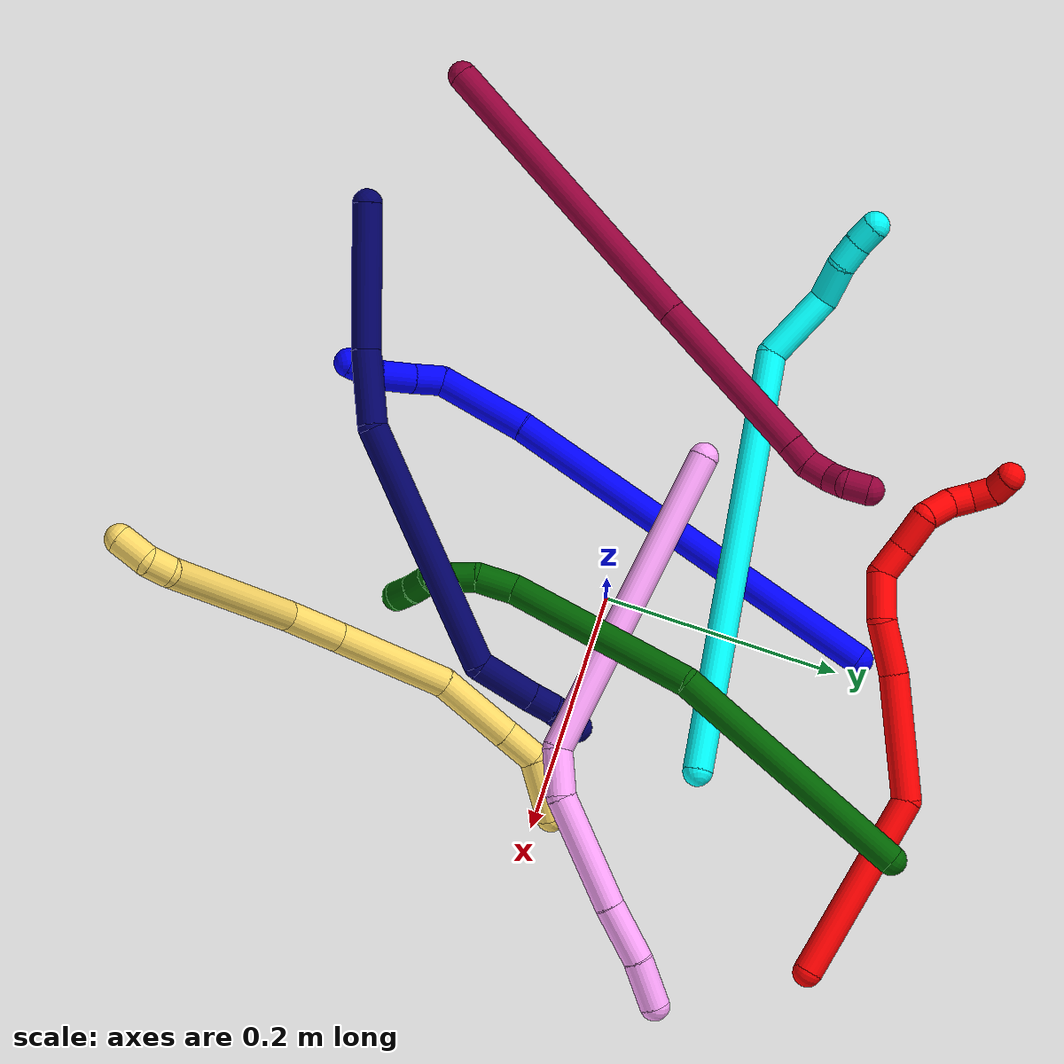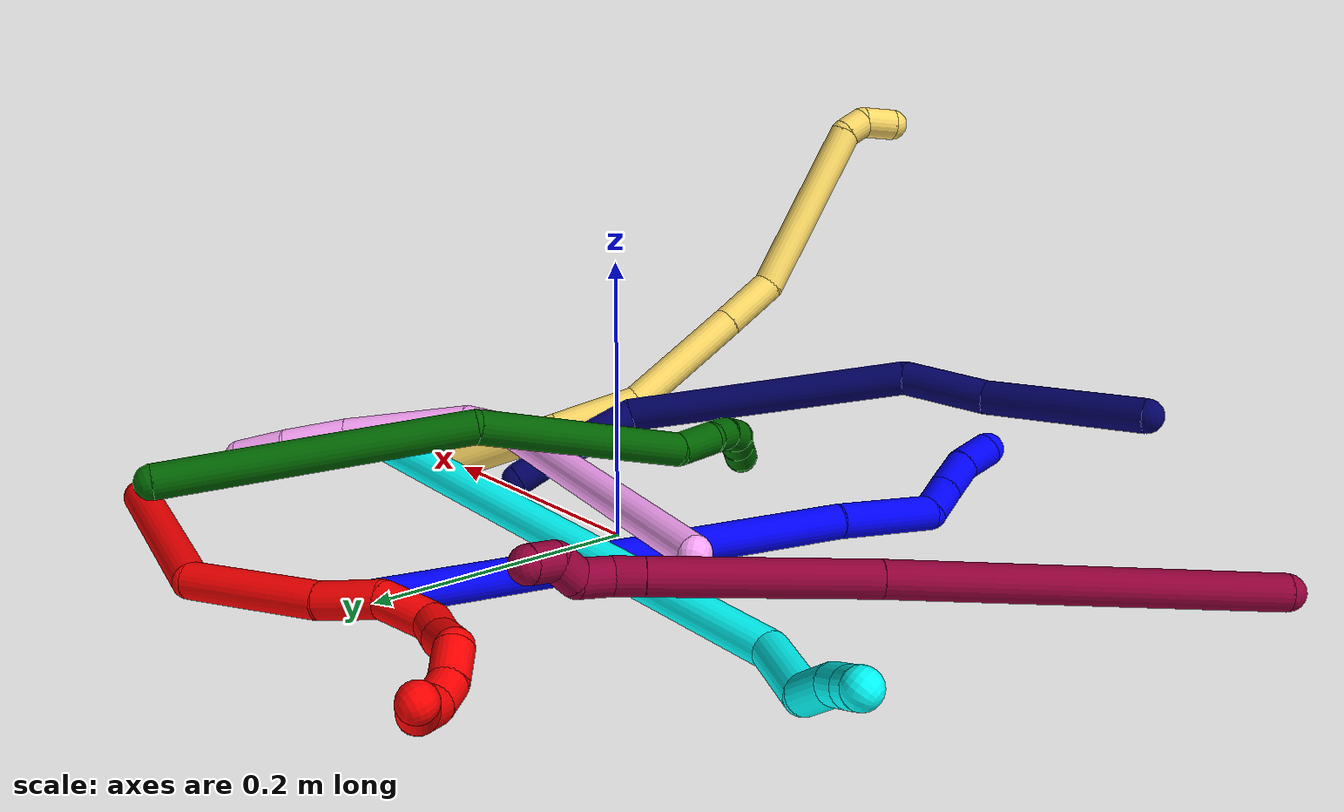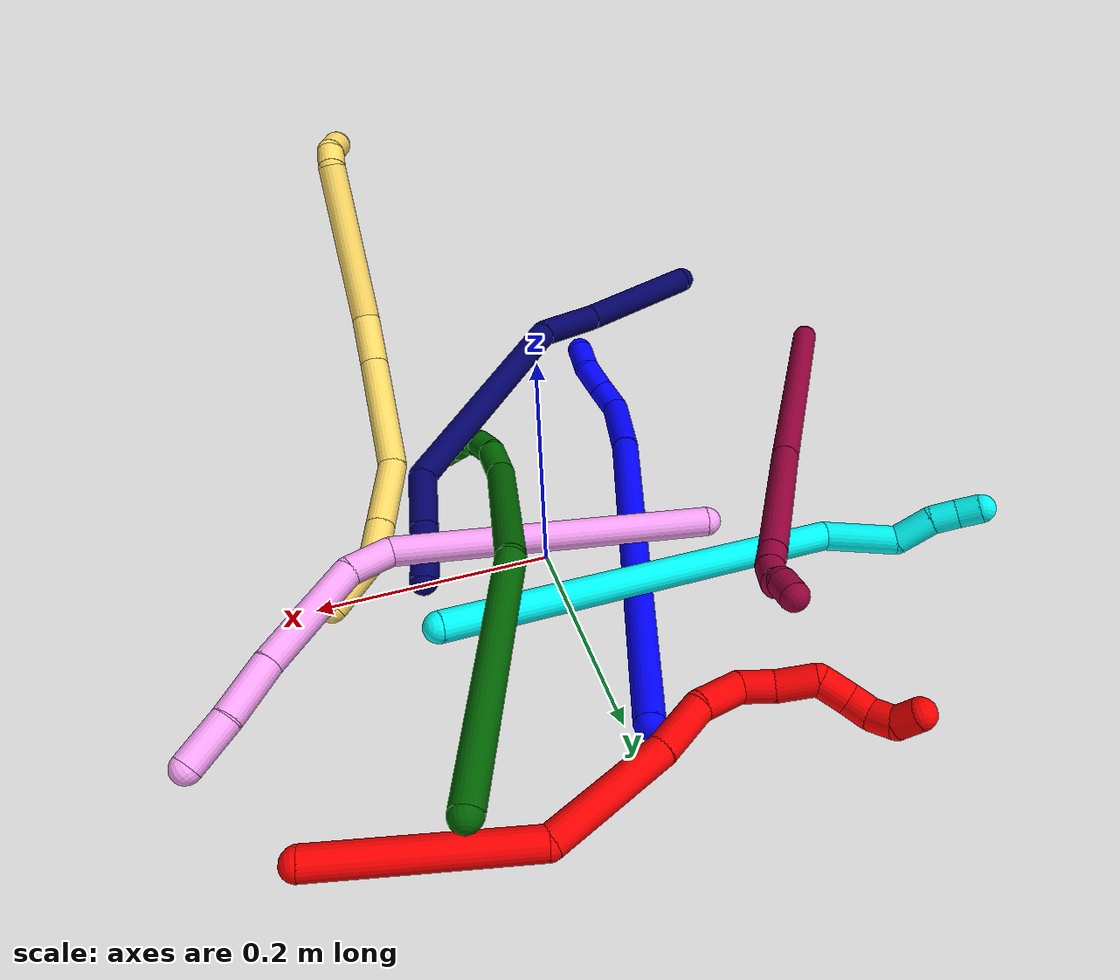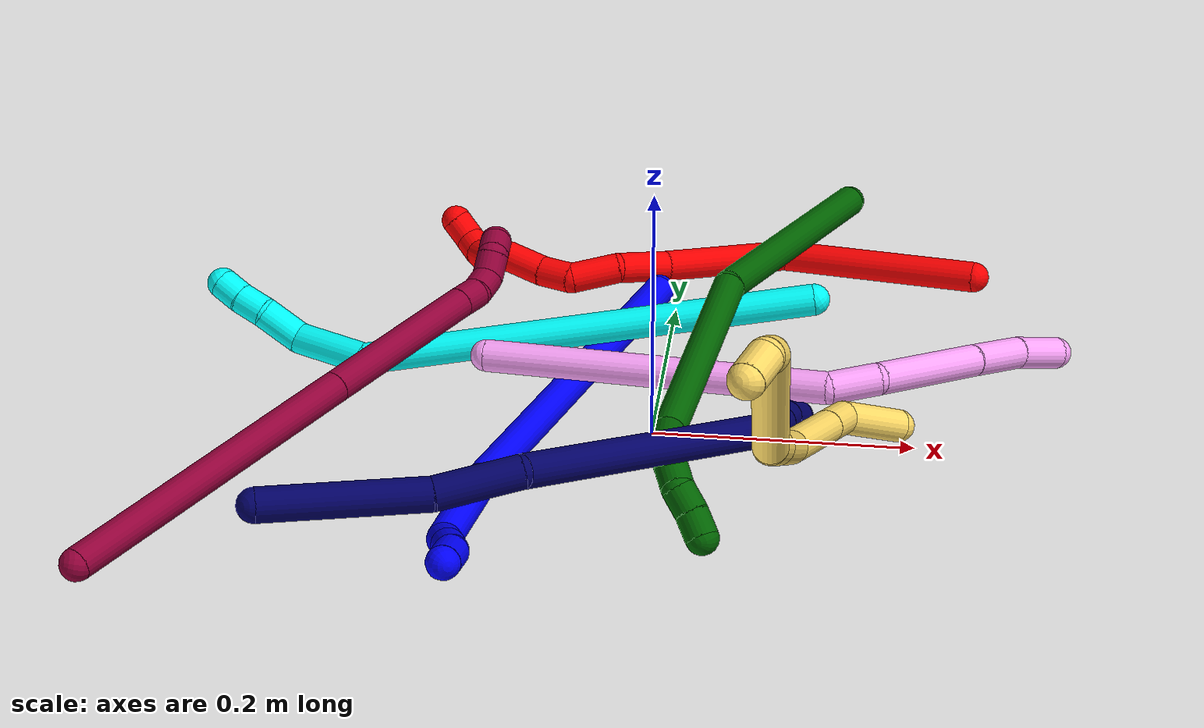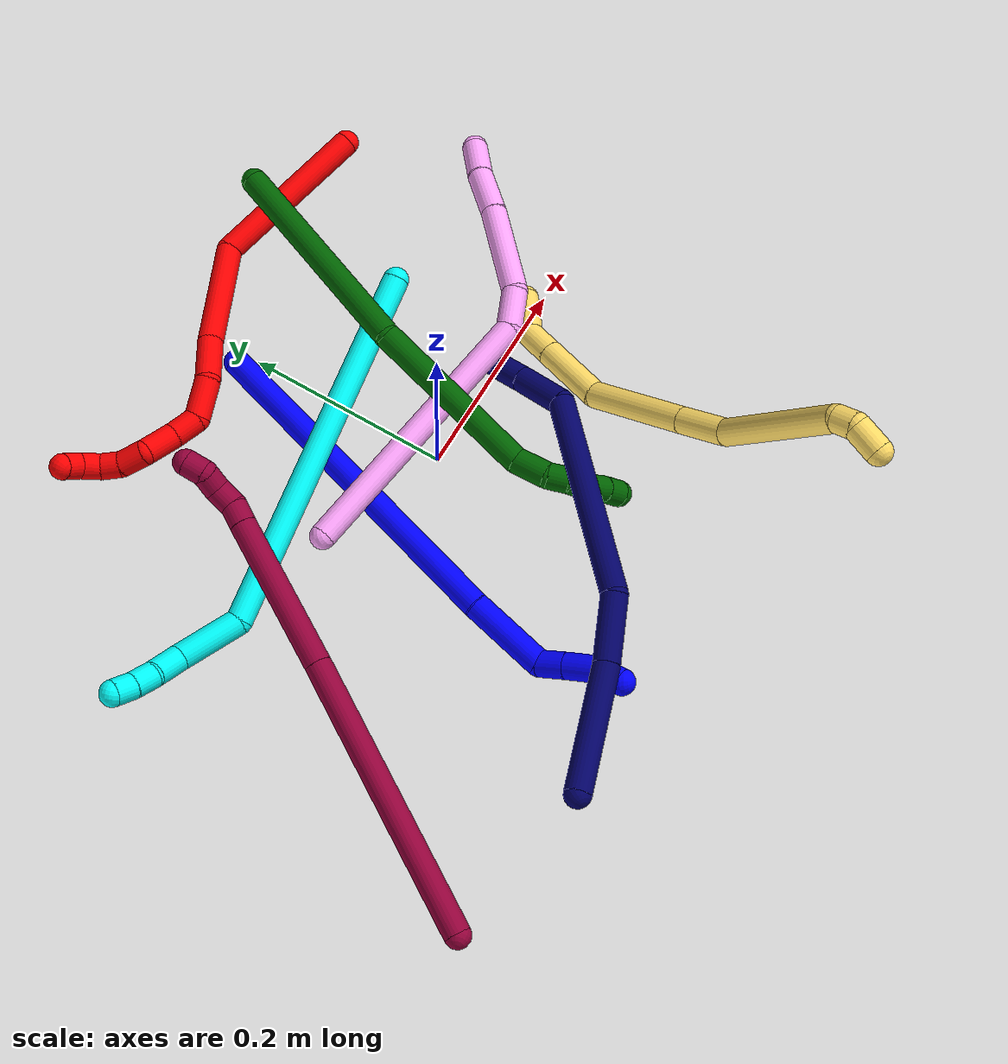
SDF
<sdf version="1.7">
 <world name="default">
  <plugin name="TubeGeneratorPlugin" filename="libtube_generator_plugin.so"/>
  <model name="photoneo_s_sensor">
   <static>1</static>
   <pose>0 0 2 1.57079 1.57079 3.14159</pose>
   <link name="link">
    <inertial><mass>0.1</mass></inertial>
    <sensor name="sensor" type="depth">
     <update_rate>30</update_rate>
     <camera>
      <horizontal_fov>1.22</horizontal_fov>
      <image><width>1920</width><height>1200</height><format>B8G8R8</format></image>
      <clip><near>0.1</near><far>4</far></clip>
      <depth_camera><output>points</output></depth_camera>
     </camera>
     <plugin name="camera_plugin" filename="libgazebo_ros_depth_camera.so">
      <baseline>0.2</baseline>
      <alwaysOn>1</alwaysOn>
      <updateRate>0.0</updateRate>
      <cameraName>camera_ir</cameraName>
      <imageTopicName>/camera/color/image_raw</imageTopicName>
      <cameraInfoTopicName>/camera/color/camera_info</cameraInfoTopicName>
      <depthImageTopicName>/camera/depth/image_raw</depthImageTopicName>
      <depthImageCameraInfoTopicName>/camera/depth/camera_info</depthImageCameraInfoTopicName>
      <pointCloudTopicName>/camera/depth/points</pointCloudTopicName>
      <frameName>fr_optical</frameName>
      <pointCloudCutoff>0.1</pointCloudCutoff>
      <pointCloudCutoffMax>2.0</pointCloudCutoffMax>
      <distortionK1>0</distortionK1>
      <distortionK2>0</distortionK2>
      <distortionK3>0</distortionK3>
      <distortionT1>0</distortionT1>
      <distortionT2>0</distortionT2>
      <CxPrime>0</CxPrime>
      <Cx>0</Cx>
      <Cy>0</Cy>
      <focalLength>0</focalLength>
      <hackBaseline>0</hackBaseline>
     </plugin>
    </sensor>
   </link>
  </model>
  <gravity>0 0 -9.8</gravity>
  <magnetic_field>6e-06 2.3e-05 -4.2e-05</magnetic_field>
  <atmosphere type="adiabatic"/>
  <physics name="default_physics" default="0" type="ode">
   <max_step_size>0.003</max_step_size>
   <real_time_factor>1</real_time_factor>
   <real_time_update_rate>1000</real_time_update_rate>
   <max_contacts>10000</max_contacts>
   <ode>
    <solver>
     <type>quick</type>
     <iters>100</iters>
     <sor>1.3</sor>
     <use_dynamic_moi_rescaling>0</use_dynamic_moi_rescaling>
    </solver>
    <constraints>
     <contact_max_correcting_vel>0</contact_max_correcting_vel>
     <contact_surface_layer>0.001</contact_surface_layer>
     <cfm>0</cfm>
     <erp>0.2</erp>
    </constraints>
   </ode>
  </physics>
  <scene><ambient>0.4 0.4 0.4 1</ambient><background>0.7 0.7 0.7 1</background><shadows>0</shadows></scene>
  <audio><device>default</device></audio>
  <spherical_coordinates>
   <surface_model>EARTH_WGS84</surface_model>
   <latitude_deg>0</latitude_deg>
   <longitude_deg>0</longitude_deg>
   <elevation>0</elevation>
   <heading_deg>0</heading_deg>
  </spherical_coordinates>
  <model name="bin">
   <static>1</static>
   <link name="bottom">
    <collision name="collision-bottom">
     <pose>0 0 -0.01 0 -0 0</pose>
     <geometry><box><size>0.8 0.6 0.02</size></box></geometry>
     <surface>
      <friction><ode><mu>100</mu><mu2>100</mu2></ode></friction>
      <contact><collide_bitmask>65535</collide_bitmask></contact>
     </surface>
    </collision>
   </link>
   <link name="west_wall">
    <collision name="collision-west_wall">
     <pose>-0.41 0 0.1 0 -0 0</pose>
     <geometry><box><size>0.02 0.6 0.2</size></box></geometry>
     <surface>
      <friction><ode><mu>100</mu><mu2>100</mu2></ode></friction>
      <contact><collide_bitmask>65535</collide_bitmask></contact>
     </surface>
    </collision>
   </link>
   <link name="east_wall">
    <collision name="collision-east_wall">
     <pose>0.41 0 0.1 0 -0 0</pose>
     <geometry><box><size>0.02 0.6 0.2</size></box></geometry>
     <surface>
      <friction><ode><mu>100</mu><mu2>100</mu2></ode></friction>
      <contact><collide_bitmask>65535</collide_bitmask></contact>
     </surface>
    </collision>
   </link>
   <link name="south_wall">
    <collision name="collision-south_wall">
     <pose>0 -0.31 0.1 0 -0 0</pose>
     <geometry><box><size>0.8 0.02 0.2</size></box></geometry>
     <surface>
      <friction><ode><mu>100</mu><mu2>100</mu2></ode></friction>
      <contact><collide_bitmask>65535</collide_bitmask></contact>
     </surface>
    </collision>
   </link>
   <link name="north_wall">
    <collision name="collision-north_wall">
     <pose>0 0.31 0.1 0 -0 0</pose>
     <geometry><box><size>0.8 0.02 0.2</size></box></geometry>
     <surface>
      <friction><ode><mu>100</mu><mu2>100</mu2></ode></friction>
      <contact><collide_bitmask>65535</collide_bitmask></contact>
     </surface>
    </collision>
   </link>
  </model>
  <model name="1">
   <static>0</static>
   <link name="1">
    <collision name="collision-cylinder-e_1_1_4">
     <pose>0.012416 -0.123575 -0.114828 2.31952 0.073472 0.168244</pose>
     <geometry><cylinder><radius>0.0125</radius><length>0.338292</length></cylinder></geometry>
     <surface>
      <friction><ode><mu>1.16</mu><mu2>1.16</mu2><slip1>0</slip1><slip2>0</slip2></ode></friction>
      <contact><ode><kp>1e+06</kp><kd>1</kd><max_vel>0</max_vel><min_depth>0.001</min_depth></ode></contact>
     </surface>
    </collision>
    <visual name="visual-cylinder-e_1_1_4">
     <pose>0.012416 -0.123575 -0.114828 2.31952 0.073472 0.168244</pose>
     <geometry><cylinder><radius>0.0125</radius><length>0.338292</length></cylinder></geometry>
     <material><ambient>0 0 1 1</ambient></material>
    </visual>
    <collision name="collision-cylinder-e_2_4_5">
     <pose>0.023035 -0.27496 -0.257169 2.35083 -0.045916 -0.109925</pose>
     <geometry><cylinder><radius>0.0125</radius><length>0.078322</length></cylinder></geometry>
     <surface>
      <friction><ode><mu>1.16</mu><mu2>1.16</mu2><slip1>0</slip1><slip2>0</slip2></ode></friction>
      <contact><ode><kp>1e+06</kp><kd>1</kd><max_vel>0</max_vel><min_depth>0.001</min_depth></ode></contact>
     </surface>
    </collision>
    <visual name="visual-cylinder-e_2_4_5">
     <pose>0.023035 -0.27496 -0.257169 2.35083 -0.045916 -0.109925</pose>
     <geometry><cylinder><radius>0.0125</radius><length>0.078322</length></cylinder></geometry>
     <material><ambient>0 0 1 1</ambient></material>
    </visual>
    <collision name="collision-cylinder-e_3_5_6">
     <pose>0.023691 -0.304545 -0.297652 3.00558 0.18525 1.87624</pose>
     <geometry><cylinder><radius>0.0125</radius><length>0.026637</length></cylinder></geometry>
     <surface>
      <friction><ode><mu>1.16</mu><mu2>1.16</mu2><slip1>0</slip1><slip2>0</slip2></ode></friction>
      <contact><ode><kp>1e+06</kp><kd>1</kd><max_vel>0</max_vel><min_depth>0.001</min_depth></ode></contact>
     </surface>
    </collision>
    <visual name="visual-cylinder-e_3_5_6">
     <pose>0.023691 -0.304545 -0.297652 3.00558 0.18525 1.87624</pose>
     <geometry><cylinder><radius>0.0125</radius><length>0.026637</length></cylinder></geometry>
     <material><ambient>0 0 1 1</ambient></material>
    </visual>
    <collision name="collision-cylinder-e_4_6_7">
     <pose>0.029297 -0.30868 -0.325108 2.9801 0.211583 1.83925</pose>
     <geometry><cylinder><radius>0.0125</radius><length>0.030024</length></cylinder></geometry>
     <surface>
      <friction><ode><mu>1.16</mu><mu2>1.16</mu2><slip1>0</slip1><slip2>0</slip2></ode></friction>
      <contact><ode><kp>1e+06</kp><kd>1</kd><max_vel>0</max_vel><min_depth>0.001</min_depth></ode></contact>
     </surface>
    </collision>
    <visual name="visual-cylinder-e_4_6_7">
     <pose>0.029297 -0.30868 -0.325108 2.9801 0.211583 1.83925</pose>
     <geometry><cylinder><radius>0.0125</radius><length>0.030024</length></cylinder></geometry>
     <material><ambient>0 0 1 1</ambient></material>
    </visual>
    <collision name="collision-cylinder-e_5_7_2">
     <pose>0.03522 -0.31723 -0.351107 2.64824 0.208887 0.788953</pose>
     <geometry><cylinder><radius>0.0125</radius><length>0.026725</length></cylinder></geometry>
     <surface>
      <friction><ode><mu>1.16</mu><mu2>1.16</mu2><slip1>0</slip1><slip2>0</slip2></ode></friction>
      <contact><ode><kp>1e+06</kp><kd>1</kd><max_vel>0</max_vel><min_depth>0.001</min_depth></ode></contact>
     </surface>
    </collision>
    <visual name="visual-cylinder-e_5_7_2">
     <pose>0.03522 -0.31723 -0.351107 2.64824 0.208887 0.788953</pose>
     <geometry><cylinder><radius>0.0125</radius><length>0.026725</length></cylinder></geometry>
     <material><ambient>0 0 1 1</ambient></material>
    </visual>
    <collision name="collision-sphere-2">
     <pose>0.037991 -0.323421 -0.36262 0 -0 0</pose>
     <geometry><sphere><radius>0.0125</radius></sphere></geometry>
     <surface>
      <friction><ode><mu>1.16</mu><mu2>1.16</mu2><slip1>0</slip1><slip2>0</slip2></ode></friction>
      <contact><ode><kp>1e+06</kp><kd>1</kd><max_vel>0</max_vel><min_depth>0.001</min_depth></ode></contact>
     </surface>
    </collision>
    <visual name="visual-sphere-2">
     <pose>0.037991 -0.323421 -0.36262 0 -0 0</pose>
     <geometry><sphere><radius>0.0125</radius></sphere></geometry>
     <material><ambient>0 0 1 1</ambient></material>
    </visual>
    <collision name="collision-sphere-7">
     <pose>0.032449 -0.31104 -0.339594 0 -0 0</pose>
     <geometry><sphere><radius>0.0125</radius></sphere></geometry>
     <surface>
      <friction><ode><mu>1.16</mu><mu2>1.16</mu2><slip1>0</slip1><slip2>0</slip2></ode></friction>
      <contact><ode><kp>1e+06</kp><kd>1</kd><max_vel>0</max_vel><min_depth>0.001</min_depth></ode></contact>
     </surface>
    </collision>
    <visual name="visual-sphere-7">
     <pose>0.032449 -0.31104 -0.339594 0 -0 0</pose>
     <geometry><sphere><radius>0.0125</radius></sphere></geometry>
     <material><ambient>0 0 1 1</ambient></material>
    </visual>
    <collision name="collision-sphere-6">
     <pose>0.026144 -0.30632 -0.310622 0 -0 0</pose>
     <geometry><sphere><radius>0.0125</radius></sphere></geometry>
     <surface>
      <friction><ode><mu>1.16</mu><mu2>1.16</mu2><slip1>0</slip1><slip2>0</slip2></ode></friction>
      <contact><ode><kp>1e+06</kp><kd>1</kd><max_vel>0</max_vel><min_depth>0.001</min_depth></ode></contact>
     </surface>
    </collision>
    <visual name="visual-sphere-6">
     <pose>0.026144 -0.30632 -0.310622 0 -0 0</pose>
     <geometry><sphere><radius>0.0125</radius></sphere></geometry>
     <material><ambient>0 0 1 1</ambient></material>
    </visual>
    <collision name="collision-sphere-5">
     <pose>0.021238 -0.30277 -0.284682 0 -0 0</pose>
     <geometry><sphere><radius>0.0125</radius></sphere></geometry>
     <surface>
      <friction><ode><mu>1.16</mu><mu2>1.16</mu2><slip1>0</slip1><slip2>0</slip2></ode></friction>
      <contact><ode><kp>1e+06</kp><kd>1</kd><max_vel>0</max_vel><min_depth>0.001</min_depth></ode></contact>
     </surface>
    </collision>
    <visual name="visual-sphere-5">
     <pose>0.021238 -0.30277 -0.284682 0 -0 0</pose>
     <geometry><sphere><radius>0.0125</radius></sphere></geometry>
     <material><ambient>0 0 1 1</ambient></material>
    </visual>
    <collision name="collision-sphere-1">
     <geometry><sphere><radius>0.0125</radius></sphere></geometry>
     <surface>
      <friction><ode><mu>1.16</mu><mu2>1.16</mu2><slip1>0</slip1><slip2>0</slip2></ode></friction>
      <contact><ode><kp>1e+06</kp><kd>1</kd><max_vel>0</max_vel><min_depth>0.001</min_depth></ode></contact>
     </surface>
    </collision>
    <visual name="visual-sphere-1">
     <geometry><sphere><radius>0.0125</radius></sphere></geometry>
     <material><ambient>0 0 1 1</ambient></material>
    </visual>
    <collision name="collision-sphere-4">
     <pose>0.024833 -0.24715 -0.229656 0 -0 0</pose>
     <geometry><sphere><radius>0.0125</radius></sphere></geometry>
     <surface>
      <friction><ode><mu>1.16</mu><mu2>1.16</mu2><slip1>0</slip1><slip2>0</slip2></ode></friction>
      <contact><ode><kp>1e+06</kp><kd>1</kd><max_vel>0</max_vel><min_depth>0.001</min_depth></ode></contact>
     </surface>
    </collision>
    <visual name="visual-sphere-4">
     <pose>0.024833 -0.24715 -0.229656 0 -0 0</pose>
     <geometry><sphere><radius>0.0125</radius></sphere></geometry>
     <material><ambient>0 0 1 1</ambient></material>
    </visual>
    <inertial>
     <pose>0.016913 -0.178396 -0.17212 0 -0 0</pose>
     <mass>0.5</mass>
     <inertia>
      <ixx>0.003775</ixx>
      <ixy>0</ixy>
      <ixz>0</ixz>
      <iyy>-0.001656</iyy>
      <iyz>0</iyz>
      <izz>0.002133</izz>
     </inertia>
    </inertial>
   </link>
   <pose>-0.015288 0.214438 0.011494 2.2758 -1.1391 2.98457</pose>
  </model>
  <model name="2">
   <static>0</static>
   <link name="2">
    <collision name="collision-cylinder-e_1_1_4">
     <pose>-0.08092 -0.004396 0.007676 0.520164 -1.46192 -0.468452</pose>
     <geometry><cylinder><radius>0.0125</radius><length>0.162805</length></cylinder></geometry>
     <surface>
      <friction><ode><mu>1.16</mu><mu2>1.16</mu2><slip1>0</slip1><slip2>0</slip2></ode></friction>
      <contact><ode><kp>1e+06</kp><kd>1</kd><max_vel>0</max_vel><min_depth>0.001</min_depth></ode></contact>
     </surface>
    </collision>
    <visual name="visual-cylinder-e_1_1_4">
     <pose>-0.08092 -0.004396 0.007676 0.520164 -1.46192 -0.468452</pose>
     <geometry><cylinder><radius>0.0125</radius><length>0.162805</length></cylinder></geometry>
     <material><ambient>1 0 0 1</ambient></material>
    </visual>
    <collision name="collision-cylinder-e_2_4_5">
     <pose>-0.207197 -0.005748 -0.011451 -3.02847 -1.03427 2.94314</pose>
     <geometry><cylinder><radius>0.0125</radius><length>0.105543</length></cylinder></geometry>
     <surface>
      <friction><ode><mu>1.16</mu><mu2>1.16</mu2><slip1>0</slip1><slip2>0</slip2></ode></friction>
      <contact><ode><kp>1e+06</kp><kd>1</kd><max_vel>0</max_vel><min_depth>0.001</min_depth></ode></contact>
     </surface>
    </collision>
    <visual name="visual-cylinder-e_2_4_5">
     <pose>-0.207197 -0.005748 -0.011451 -3.02847 -1.03427 2.94314</pose>
     <geometry><cylinder><radius>0.0125</radius><length>0.105543</length></cylinder></geometry>
     <material><ambient>1 0 0 1</ambient></material>
    </visual>
    <collision name="collision-cylinder-e_3_5_6">
     <pose>-0.269863 -0.002902 -0.05255 3.12765 -0.880353 -3.112</pose>
     <geometry><cylinder><radius>0.0125</radius><length>0.044903</length></cylinder></geometry>
     <surface>
      <friction><ode><mu>1.16</mu><mu2>1.16</mu2><slip1>0</slip1><slip2>0</slip2></ode></friction>
      <contact><ode><kp>1e+06</kp><kd>1</kd><max_vel>0</max_vel><min_depth>0.001</min_depth></ode></contact>
     </surface>
    </collision>
    <visual name="visual-cylinder-e_3_5_6">
     <pose>-0.269863 -0.002902 -0.05255 3.12765 -0.880353 -3.112</pose>
     <geometry><cylinder><radius>0.0125</radius><length>0.044903</length></cylinder></geometry>
     <material><ambient>1 0 0 1</ambient></material>
    </visual>
    <collision name="collision-cylinder-e_4_6_7">
     <pose>-0.305319 0.001082 -0.073897 -2.60605 -1.14649 2.33786</pose>
     <geometry><cylinder><radius>0.0125</radius><length>0.039826</length></cylinder></geometry>
     <surface>
      <friction><ode><mu>1.16</mu><mu2>1.16</mu2><slip1>0</slip1><slip2>0</slip2></ode></friction>
      <contact><ode><kp>1e+06</kp><kd>1</kd><max_vel>0</max_vel><min_depth>0.001</min_depth></ode></contact>
     </surface>
    </collision>
    <visual name="visual-cylinder-e_4_6_7">
     <pose>-0.305319 0.001082 -0.073897 -2.60605 -1.14649 2.33786</pose>
     <geometry><cylinder><radius>0.0125</radius><length>0.039826</length></cylinder></geometry>
     <material><ambient>1 0 0 1</ambient></material>
    </visual>
    <collision name="collision-cylinder-e_5_7_8">
     <pose>-0.33665 0.003165 -0.078314 0.673191 -1.32063 -0.530675</pose>
     <geometry><cylinder><radius>0.0125</radius><length>0.027216</length></cylinder></geometry>
     <surface>
      <friction><ode><mu>1.16</mu><mu2>1.16</mu2><slip1>0</slip1><slip2>0</slip2></ode></friction>
      <contact><ode><kp>1e+06</kp><kd>1</kd><max_vel>0</max_vel><min_depth>0.001</min_depth></ode></contact>
     </surface>
    </collision>
    <visual name="visual-cylinder-e_5_7_8">
     <pose>-0.33665 0.003165 -0.078314 0.673191 -1.32063 -0.530675</pose>
     <geometry><cylinder><radius>0.0125</radius><length>0.027216</length></cylinder></geometry>
     <material><ambient>1 0 0 1</ambient></material>
    </visual>
    <collision name="collision-cylinder-e_6_8_9">
     <pose>-0.365186 -0.004311 -0.073847 1.24224 -1.21645 -0.924507</pose>
     <geometry><cylinder><radius>0.0125</radius><length>0.032736</length></cylinder></geometry>
     <surface>
      <friction><ode><mu>1.16</mu><mu2>1.16</mu2><slip1>0</slip1><slip2>0</slip2></ode></friction>
      <contact><ode><kp>1e+06</kp><kd>1</kd><max_vel>0</max_vel><min_depth>0.001</min_depth></ode></contact>
     </surface>
    </collision>
    <visual name="visual-cylinder-e_6_8_9">
     <pose>-0.365186 -0.004311 -0.073847 1.24224 -1.21645 -0.924507</pose>
     <geometry><cylinder><radius>0.0125</radius><length>0.032736</length></cylinder></geometry>
     <material><ambient>1 0 0 1</ambient></material>
    </visual>
    <collision name="collision-cylinder-e_7_9_10">
     <pose>-0.390588 -0.007269 -0.064028 -0.29399 -0.877886 0.138805</pose>
     <geometry><cylinder><radius>0.0125</radius><length>0.026128</length></cylinder></geometry>
     <surface>
      <friction><ode><mu>1.16</mu><mu2>1.16</mu2><slip1>0</slip1><slip2>0</slip2></ode></friction>
      <contact><ode><kp>1e+06</kp><kd>1</kd><max_vel>0</max_vel><min_depth>0.001</min_depth></ode></contact>
     </surface>
    </collision>
    <visual name="visual-cylinder-e_7_9_10">
     <pose>-0.390588 -0.007269 -0.064028 -0.29399 -0.877886 0.138805</pose>
     <geometry><cylinder><radius>0.0125</radius><length>0.026128</length></cylinder></geometry>
     <material><ambient>1 0 0 1</ambient></material>
    </visual>
    <collision name="collision-cylinder-e_8_10_11">
     <pose>-0.407008 -0.005749 -0.048342 0.116154 -0.687838 -0.041642</pose>
     <geometry><cylinder><radius>0.0125</radius><length>0.020064</length></cylinder></geometry>
     <surface>
      <friction><ode><mu>1.16</mu><mu2>1.16</mu2><slip1>0</slip1><slip2>0</slip2></ode></friction>
      <contact><ode><kp>1e+06</kp><kd>1</kd><max_vel>0</max_vel><min_depth>0.001</min_depth></ode></contact>
     </surface>
    </collision>
    <visual name="visual-cylinder-e_8_10_11">
     <pose>-0.407008 -0.005749 -0.048342 0.116154 -0.687838 -0.041642</pose>
     <geometry><cylinder><radius>0.0125</radius><length>0.020064</length></cylinder></geometry>
     <material><ambient>1 0 0 1</ambient></material>
    </visual>
    <collision name="collision-cylinder-e_9_11_12">
     <pose>-0.419613 -0.011447 -0.034206 0.640646 -0.660303 -0.226404</pose>
     <geometry><cylinder><radius>0.0125</radius><length>0.020333</length></cylinder></geometry>
     <surface>
      <friction><ode><mu>1.16</mu><mu2>1.16</mu2><slip1>0</slip1><slip2>0</slip2></ode></friction>
      <contact><ode><kp>1e+06</kp><kd>1</kd><max_vel>0</max_vel><min_depth>0.001</min_depth></ode></contact>
     </surface>
    </collision>
    <visual name="visual-cylinder-e_9_11_12">
     <pose>-0.419613 -0.011447 -0.034206 0.640646 -0.660303 -0.226404</pose>
     <geometry><cylinder><radius>0.0125</radius><length>0.020333</length></cylinder></geometry>
     <material><ambient>1 0 0 1</ambient></material>
    </visual>
    <collision name="collision-cylinder-e_10_12_2">
     <pose>-0.432371 -0.024082 -0.027009 1.47416 -0.691857 -0.632388</pose>
     <geometry><cylinder><radius>0.0125</radius><length>0.020448</length></cylinder></geometry>
     <surface>
      <friction><ode><mu>1.16</mu><mu2>1.16</mu2><slip1>0</slip1><slip2>0</slip2></ode></friction>
      <contact><ode><kp>1e+06</kp><kd>1</kd><max_vel>0</max_vel><min_depth>0.001</min_depth></ode></contact>
     </surface>
    </collision>
    <visual name="visual-cylinder-e_10_12_2">
     <pose>-0.432371 -0.024082 -0.027009 1.47416 -0.691857 -0.632388</pose>
     <geometry><cylinder><radius>0.0125</radius><length>0.020448</length></cylinder></geometry>
     <material><ambient>1 0 0 1</ambient></material>
    </visual>
    <collision name="collision-sphere-2">
     <pose>-0.438894 -0.031918 -0.026249 0 -0 0</pose>
     <geometry><sphere><radius>0.0125</radius></sphere></geometry>
     <surface>
      <friction><ode><mu>1.16</mu><mu2>1.16</mu2><slip1>0</slip1><slip2>0</slip2></ode></friction>
      <contact><ode><kp>1e+06</kp><kd>1</kd><max_vel>0</max_vel><min_depth>0.001</min_depth></ode></contact>
     </surface>
    </collision>
    <visual name="visual-sphere-2">
     <pose>-0.438894 -0.031918 -0.026249 0 -0 0</pose>
     <geometry><sphere><radius>0.0125</radius></sphere></geometry>
     <material><ambient>1 0 0 1</ambient></material>
    </visual>
    <collision name="collision-sphere-12">
     <pose>-0.425849 -0.016246 -0.027769 0 -0 0</pose>
     <geometry><sphere><radius>0.0125</radius></sphere></geometry>
     <surface>
      <friction><ode><mu>1.16</mu><mu2>1.16</mu2><slip1>0</slip1><slip2>0</slip2></ode></friction>
      <contact><ode><kp>1e+06</kp><kd>1</kd><max_vel>0</max_vel><min_depth>0.001</min_depth></ode></contact>
     </surface>
    </collision>
    <visual name="visual-sphere-12">
     <pose>-0.425849 -0.016246 -0.027769 0 -0 0</pose>
     <geometry><sphere><radius>0.0125</radius></sphere></geometry>
     <material><ambient>1 0 0 1</ambient></material>
    </visual>
    <collision name="collision-sphere-11">
     <pose>-0.413377 -0.006647 -0.040644 0 -0 0</pose>
     <geometry><sphere><radius>0.0125</radius></sphere></geometry>
     <surface>
      <friction><ode><mu>1.16</mu><mu2>1.16</mu2><slip1>0</slip1><slip2>0</slip2></ode></friction>
      <contact><ode><kp>1e+06</kp><kd>1</kd><max_vel>0</max_vel><min_depth>0.001</min_depth></ode></contact>
     </surface>
    </collision>
    <visual name="visual-sphere-11">
     <pose>-0.413377 -0.006647 -0.040644 0 -0 0</pose>
     <geometry><sphere><radius>0.0125</radius></sphere></geometry>
     <material><ambient>1 0 0 1</ambient></material>
    </visual>
    <collision name="collision-sphere-10">
     <pose>-0.400639 -0.004851 -0.056041 0 -0 0</pose>
     <geometry><sphere><radius>0.0125</radius></sphere></geometry>
     <surface>
      <friction><ode><mu>1.16</mu><mu2>1.16</mu2><slip1>0</slip1><slip2>0</slip2></ode></friction>
      <contact><ode><kp>1e+06</kp><kd>1</kd><max_vel>0</max_vel><min_depth>0.001</min_depth></ode></contact>
     </surface>
    </collision>
    <visual name="visual-sphere-10">
     <pose>-0.400639 -0.004851 -0.056041 0 -0 0</pose>
     <geometry><sphere><radius>0.0125</radius></sphere></geometry>
     <material><ambient>1 0 0 1</ambient></material>
    </visual>
    <collision name="collision-sphere-9">
     <pose>-0.380537 -0.009687 -0.072015 0 -0 0</pose>
     <geometry><sphere><radius>0.0125</radius></sphere></geometry>
     <surface>
      <friction><ode><mu>1.16</mu><mu2>1.16</mu2><slip1>0</slip1><slip2>0</slip2></ode></friction>
      <contact><ode><kp>1e+06</kp><kd>1</kd><max_vel>0</max_vel><min_depth>0.001</min_depth></ode></contact>
     </surface>
    </collision>
    <visual name="visual-sphere-9">
     <pose>-0.380537 -0.009687 -0.072015 0 -0 0</pose>
     <geometry><sphere><radius>0.0125</radius></sphere></geometry>
     <material><ambient>1 0 0 1</ambient></material>
    </visual>
    <collision name="collision-sphere-4">
     <pose>-0.161841 -0.008793 0.015351 0 -0 0</pose>
     <geometry><sphere><radius>0.0125</radius></sphere></geometry>
     <surface>
      <friction><ode><mu>1.16</mu><mu2>1.16</mu2><slip1>0</slip1><slip2>0</slip2></ode></friction>
      <contact><ode><kp>1e+06</kp><kd>1</kd><max_vel>0</max_vel><min_depth>0.001</min_depth></ode></contact>
     </surface>
    </collision>
    <visual name="visual-sphere-4">
     <pose>-0.161841 -0.008793 0.015351 0 -0 0</pose>
     <geometry><sphere><radius>0.0125</radius></sphere></geometry>
     <material><ambient>1 0 0 1</ambient></material>
    </visual>
    <collision name="collision-sphere-1">
     <geometry><sphere><radius>0.0125</radius></sphere></geometry>
     <surface>
      <friction><ode><mu>1.16</mu><mu2>1.16</mu2><slip1>0</slip1><slip2>0</slip2></ode></friction>
      <contact><ode><kp>1e+06</kp><kd>1</kd><max_vel>0</max_vel><min_depth>0.001</min_depth></ode></contact>
     </surface>
    </collision>
    <visual name="visual-sphere-1">
     <geometry><sphere><radius>0.0125</radius></sphere></geometry>
     <material><ambient>1 0 0 1</ambient></material>
    </visual>
    <collision name="collision-sphere-8">
     <pose>-0.349835 0.001064 -0.07568 0 -0 0</pose>
     <geometry><sphere><radius>0.0125</radius></sphere></geometry>
     <surface>
      <friction><ode><mu>1.16</mu><mu2>1.16</mu2><slip1>0</slip1><slip2>0</slip2></ode></friction>
      <contact><ode><kp>1e+06</kp><kd>1</kd><max_vel>0</max_vel><min_depth>0.001</min_depth></ode></contact>
     </surface>
    </collision>
    <visual name="visual-sphere-8">
     <pose>-0.349835 0.001064 -0.07568 0 -0 0</pose>
     <geometry><sphere><radius>0.0125</radius></sphere></geometry>
     <material><ambient>1 0 0 1</ambient></material>
    </visual>
    <collision name="collision-sphere-5">
     <pose>-0.252554 -0.002703 -0.038252 0 -0 0</pose>
     <geometry><sphere><radius>0.0125</radius></sphere></geometry>
     <surface>
      <friction><ode><mu>1.16</mu><mu2>1.16</mu2><slip1>0</slip1><slip2>0</slip2></ode></friction>
      <contact><ode><kp>1e+06</kp><kd>1</kd><max_vel>0</max_vel><min_depth>0.001</min_depth></ode></contact>
     </surface>
    </collision>
    <visual name="visual-sphere-5">
     <pose>-0.252554 -0.002703 -0.038252 0 -0 0</pose>
     <geometry><sphere><radius>0.0125</radius></sphere></geometry>
     <material><ambient>1 0 0 1</ambient></material>
    </visual>
    <collision name="collision-sphere-6">
     <pose>-0.287172 -0.003102 -0.066847 0 -0 0</pose>
     <geometry><sphere><radius>0.0125</radius></sphere></geometry>
     <surface>
      <friction><ode><mu>1.16</mu><mu2>1.16</mu2><slip1>0</slip1><slip2>0</slip2></ode></friction>
      <contact><ode><kp>1e+06</kp><kd>1</kd><max_vel>0</max_vel><min_depth>0.001</min_depth></ode></contact>
     </surface>
    </collision>
    <visual name="visual-sphere-6">
     <pose>-0.287172 -0.003102 -0.066847 0 -0 0</pose>
     <geometry><sphere><radius>0.0125</radius></sphere></geometry>
     <material><ambient>1 0 0 1</ambient></material>
    </visual>
    <collision name="collision-sphere-7">
     <pose>-0.323466 0.005265 -0.080947 0 -0 0</pose>
     <geometry><sphere><radius>0.0125</radius></sphere></geometry>
     <surface>
      <friction><ode><mu>1.16</mu><mu2>1.16</mu2><slip1>0</slip1><slip2>0</slip2></ode></friction>
      <contact><ode><kp>1e+06</kp><kd>1</kd><max_vel>0</max_vel><min_depth>0.001</min_depth></ode></contact>
     </surface>
    </collision>
    <visual name="visual-sphere-7">
     <pose>-0.323466 0.005265 -0.080947 0 -0 0</pose>
     <geometry><sphere><radius>0.0125</radius></sphere></geometry>
     <material><ambient>1 0 0 1</ambient></material>
    </visual>
    <inertial>
     <pose>-0.232361 -0.00499 -0.027402 0 -0 0</pose>
     <mass>0.5</mass>
     <inertia><ixx>-6e-05</ixx><ixy>0</ixy><ixz>0</ixz><iyy>0.000484</iyy><iyz>0</iyz><izz>0.00049</izz></inertia>
    </inertial>
   </link>
   <pose>0.24268 0.252414 0.01929 -1.89917 -0.064052 -0.11235</pose>
  </model>
  <model name="3">
   <static>0</static>
   <link name="3">
    <collision name="collision-cylinder-e_1_1_4">
     <pose>-0.064739 0.025564 0.164972 -0.153739 -0.369942 0.028821</pose>
     <geometry><cylinder><radius>0.0125</radius><length>0.358108</length></cylinder></geometry>
     <surface>
      <friction><ode><mu>1.16</mu><mu2>1.16</mu2><slip1>0</slip1><slip2>0</slip2></ode></friction>
      <contact><ode><kp>1e+06</kp><kd>1</kd><max_vel>0</max_vel><min_depth>0.001</min_depth></ode></contact>
     </surface>
    </collision>
    <visual name="visual-cylinder-e_1_1_4">
     <pose>-0.064739 0.025564 0.164972 -0.153739 -0.369942 0.028821</pose>
     <geometry><cylinder><radius>0.0125</radius><length>0.358108</length></cylinder></geometry>
     <material><ambient>0.003922 1 0.996078 1</ambient></material>
    </visual>
    <collision name="collision-cylinder-e_2_4_5">
     <pose>-0.153794 0.046012 0.34986 0.251473 -0.868836 -0.117163</pose>
     <geometry><cylinder><radius>0.0125</radius><length>0.063691</length></cylinder></geometry>
     <surface>
      <friction><ode><mu>1.16</mu><mu2>1.16</mu2><slip1>0</slip1><slip2>0</slip2></ode></friction>
      <contact><ode><kp>1e+06</kp><kd>1</kd><max_vel>0</max_vel><min_depth>0.001</min_depth></ode></contact>
     </surface>
    </collision>
    <visual name="visual-cylinder-e_2_4_5">
     <pose>-0.153794 0.046012 0.34986 0.251473 -0.868836 -0.117163</pose>
     <geometry><cylinder><radius>0.0125</radius><length>0.063691</length></cylinder></geometry>
     <material><ambient>0.003922 1 0.996078 1</ambient></material>
    </visual>
    <collision name="collision-cylinder-e_3_5_6">
     <pose>-0.192591 0.047801 0.376705 -0.783754 -0.976614 0.432195</pose>
     <geometry><cylinder><radius>0.0125</radius><length>0.03495</length></cylinder></geometry>
     <surface>
      <friction><ode><mu>1.16</mu><mu2>1.16</mu2><slip1>0</slip1><slip2>0</slip2></ode></friction>
      <contact><ode><kp>1e+06</kp><kd>1</kd><max_vel>0</max_vel><min_depth>0.001</min_depth></ode></contact>
     </surface>
    </collision>
    <visual name="visual-cylinder-e_3_5_6">
     <pose>-0.192591 0.047801 0.376705 -0.783754 -0.976614 0.432195</pose>
     <geometry><cylinder><radius>0.0125</radius><length>0.03495</length></cylinder></geometry>
     <material><ambient>0.003922 1 0.996078 1</ambient></material>
    </visual>
    <collision name="collision-cylinder-e_4_6_7">
     <pose>-0.216958 0.056275 0.389042 -0.282159 -1.05313 0.164744</pose>
     <geometry><cylinder><radius>0.0125</radius><length>0.022756</length></cylinder></geometry>
     <surface>
      <friction><ode><mu>1.16</mu><mu2>1.16</mu2><slip1>0</slip1><slip2>0</slip2></ode></friction>
      <contact><ode><kp>1e+06</kp><kd>1</kd><max_vel>0</max_vel><min_depth>0.001</min_depth></ode></contact>
     </surface>
    </collision>
    <visual name="visual-cylinder-e_4_6_7">
     <pose>-0.216958 0.056275 0.389042 -0.282159 -1.05313 0.164744</pose>
     <geometry><cylinder><radius>0.0125</radius><length>0.022756</length></cylinder></geometry>
     <material><ambient>0.003922 1 0.996078 1</ambient></material>
    </visual>
    <collision name="collision-cylinder-e_5_7_2">
     <pose>-0.236327 0.058835 0.398208 -0.258059 -1.18176 0.173642</pose>
     <geometry><cylinder><radius>0.0125</radius><length>0.020495</length></cylinder></geometry>
     <surface>
      <friction><ode><mu>1.16</mu><mu2>1.16</mu2><slip1>0</slip1><slip2>0</slip2></ode></friction>
      <contact><ode><kp>1e+06</kp><kd>1</kd><max_vel>0</max_vel><min_depth>0.001</min_depth></ode></contact>
     </surface>
    </collision>
    <visual name="visual-cylinder-e_5_7_2">
     <pose>-0.236327 0.058835 0.398208 -0.258059 -1.18176 0.173642</pose>
     <geometry><cylinder><radius>0.0125</radius><length>0.020495</length></cylinder></geometry>
     <material><ambient>0.003922 1 0.996078 1</ambient></material>
    </visual>
    <collision name="collision-sphere-2">
     <pose>-0.245809 0.059827 0.401966 0 -0 0</pose>
     <geometry><sphere><radius>0.0125</radius></sphere></geometry>
     <surface>
      <friction><ode><mu>1.16</mu><mu2>1.16</mu2><slip1>0</slip1><slip2>0</slip2></ode></friction>
      <contact><ode><kp>1e+06</kp><kd>1</kd><max_vel>0</max_vel><min_depth>0.001</min_depth></ode></contact>
     </surface>
    </collision>
    <visual name="visual-sphere-2">
     <pose>-0.245809 0.059827 0.401966 0 -0 0</pose>
     <geometry><sphere><radius>0.0125</radius></sphere></geometry>
     <material><ambient>0.003922 1 0.996078 1</ambient></material>
    </visual>
    <collision name="collision-sphere-7">
     <pose>-0.226846 0.057843 0.39445 0 -0 0</pose>
     <geometry><sphere><radius>0.0125</radius></sphere></geometry>
     <surface>
      <friction><ode><mu>1.16</mu><mu2>1.16</mu2><slip1>0</slip1><slip2>0</slip2></ode></friction>
      <contact><ode><kp>1e+06</kp><kd>1</kd><max_vel>0</max_vel><min_depth>0.001</min_depth></ode></contact>
     </surface>
    </collision>
    <visual name="visual-sphere-7">
     <pose>-0.226846 0.057843 0.39445 0 -0 0</pose>
     <geometry><sphere><radius>0.0125</radius></sphere></geometry>
     <material><ambient>0.003922 1 0.996078 1</ambient></material>
    </visual>
    <collision name="collision-sphere-6">
     <pose>-0.207071 0.054708 0.383634 0 -0 0</pose>
     <geometry><sphere><radius>0.0125</radius></sphere></geometry>
     <surface>
      <friction><ode><mu>1.16</mu><mu2>1.16</mu2><slip1>0</slip1><slip2>0</slip2></ode></friction>
      <contact><ode><kp>1e+06</kp><kd>1</kd><max_vel>0</max_vel><min_depth>0.001</min_depth></ode></contact>
     </surface>
    </collision>
    <visual name="visual-sphere-6">
     <pose>-0.207071 0.054708 0.383634 0 -0 0</pose>
     <geometry><sphere><radius>0.0125</radius></sphere></geometry>
     <material><ambient>0.003922 1 0.996078 1</ambient></material>
    </visual>
    <collision name="collision-sphere-5">
     <pose>-0.178111 0.040895 0.369776 0 -0 0</pose>
     <geometry><sphere><radius>0.0125</radius></sphere></geometry>
     <surface>
      <friction><ode><mu>1.16</mu><mu2>1.16</mu2><slip1>0</slip1><slip2>0</slip2></ode></friction>
      <contact><ode><kp>1e+06</kp><kd>1</kd><max_vel>0</max_vel><min_depth>0.001</min_depth></ode></contact>
     </surface>
    </collision>
    <visual name="visual-sphere-5">
     <pose>-0.178111 0.040895 0.369776 0 -0 0</pose>
     <geometry><sphere><radius>0.0125</radius></sphere></geometry>
     <material><ambient>0.003922 1 0.996078 1</ambient></material>
    </visual>
    <collision name="collision-sphere-1">
     <geometry><sphere><radius>0.0125</radius></sphere></geometry>
     <surface>
      <friction><ode><mu>1.16</mu><mu2>1.16</mu2><slip1>0</slip1><slip2>0</slip2></ode></friction>
      <contact><ode><kp>1e+06</kp><kd>1</kd><max_vel>0</max_vel><min_depth>0.001</min_depth></ode></contact>
     </surface>
    </collision>
    <visual name="visual-sphere-1">
     <geometry><sphere><radius>0.0125</radius></sphere></geometry>
     <material><ambient>0.003922 1 0.996078 1</ambient></material>
    </visual>
    <collision name="collision-sphere-4">
     <pose>-0.129478 0.051129 0.329943 0 -0 0</pose>
     <geometry><sphere><radius>0.0125</radius></sphere></geometry>
     <surface>
      <friction><ode><mu>1.16</mu><mu2>1.16</mu2><slip1>0</slip1><slip2>0</slip2></ode></friction>
      <contact><ode><kp>1e+06</kp><kd>1</kd><max_vel>0</max_vel><min_depth>0.001</min_depth></ode></contact>
     </surface>
    </collision>
    <visual name="visual-sphere-4">
     <pose>-0.129478 0.051129 0.329943 0 -0 0</pose>
     <geometry><sphere><radius>0.0125</radius></sphere></geometry>
     <material><ambient>0.003922 1 0.996078 1</ambient></material>
    </visual>
    <inertial>
     <pose>-0.098981 0.032485 0.223082 0 -0 0</pose>
     <mass>0.5</mass>
     <inertia>
      <ixx>0.003683</ixx>
      <ixy>0</ixy>
      <ixz>0</ixz>
      <iyy>0.003939</iyy>
      <iyz>0</iyz>
      <izz>0.000899</izz>
     </inertia>
    </inertial>
   </link>
   <pose>0.115704 0.115672 0.061753 2.16121 0.566778 -0.887806</pose>
  </model>
  <model name="4">
   <static>0</static>
   <link name="4">
    <collision name="collision-cylinder-e_1_1_4">
     <pose>0.112758 0.026613 0.068815 -0.369014 0.99138 -0.201148</pose>
     <geometry><cylinder><radius>0.0125</radius><length>0.269504</length></cylinder></geometry>
     <surface>
      <friction><ode><mu>1.16</mu><mu2>1.16</mu2><slip1>0</slip1><slip2>0</slip2></ode></friction>
      <contact><ode><kp>1e+06</kp><kd>1</kd><max_vel>0</max_vel><min_depth>0.001</min_depth></ode></contact>
     </surface>
    </collision>
    <visual name="visual-cylinder-e_1_1_4">
     <pose>0.112758 0.026613 0.068815 -0.369014 0.99138 -0.201148</pose>
     <geometry><cylinder><radius>0.0125</radius><length>0.269504</length></cylinder></geometry>
     <material><ambient>1 0.65098 0.996078 1</ambient></material>
    </visual>
    <collision name="collision-cylinder-e_2_4_5">
     <pose>0.241209 0.064983 0.140675 -1.31732 0.91213 -0.725718</pose>
     <geometry><cylinder><radius>0.0125</radius><length>0.039687</length></cylinder></geometry>
     <surface>
      <friction><ode><mu>1.16</mu><mu2>1.16</mu2><slip1>0</slip1><slip2>0</slip2></ode></friction>
      <contact><ode><kp>1e+06</kp><kd>1</kd><max_vel>0</max_vel><min_depth>0.001</min_depth></ode></contact>
     </surface>
    </collision>
    <visual name="visual-cylinder-e_2_4_5">
     <pose>0.241209 0.064983 0.140675 -1.31732 0.91213 -0.725718</pose>
     <geometry><cylinder><radius>0.0125</radius><length>0.039687</length></cylinder></geometry>
     <material><ambient>1 0.65098 0.996078 1</ambient></material>
    </visual>
    <collision name="collision-cylinder-e_3_5_6">
     <pose>0.292864 0.108201 0.132251 -1.92042 0.821038 -1.11283</pose>
     <geometry><cylinder><radius>0.0125</radius><length>0.098279</length></cylinder></geometry>
     <surface>
      <friction><ode><mu>1.16</mu><mu2>1.16</mu2><slip1>0</slip1><slip2>0</slip2></ode></friction>
      <contact><ode><kp>1e+06</kp><kd>1</kd><max_vel>0</max_vel><min_depth>0.001</min_depth></ode></contact>
     </surface>
    </collision>
    <visual name="visual-cylinder-e_3_5_6">
     <pose>0.292864 0.108201 0.132251 -1.92042 0.821038 -1.11283</pose>
     <geometry><cylinder><radius>0.0125</radius><length>0.098279</length></cylinder></geometry>
     <material><ambient>1 0.65098 0.996078 1</ambient></material>
    </visual>
    <collision name="collision-cylinder-e_4_6_7">
     <pose>0.346783 0.155473 0.112895 -2.03342 0.79348 -1.19039</pose>
     <geometry><cylinder><radius>0.0125</radius><length>0.050381</length></cylinder></geometry>
     <surface>
      <friction><ode><mu>1.16</mu><mu2>1.16</mu2><slip1>0</slip1><slip2>0</slip2></ode></friction>
      <contact><ode><kp>1e+06</kp><kd>1</kd><max_vel>0</max_vel><min_depth>0.001</min_depth></ode></contact>
     </surface>
    </collision>
    <visual name="visual-cylinder-e_4_6_7">
     <pose>0.346783 0.155473 0.112895 -2.03342 0.79348 -1.19039</pose>
     <geometry><cylinder><radius>0.0125</radius><length>0.050381</length></cylinder></geometry>
     <material><ambient>1 0.65098 0.996078 1</ambient></material>
    </visual>
    <collision name="collision-cylinder-e_5_7_2">
     <pose>0.381806 0.182302 0.099405 -2.04132 0.943947 -1.38827</pose>
     <geometry><cylinder><radius>0.0125</radius><length>0.042149</length></cylinder></geometry>
     <surface>
      <friction><ode><mu>1.16</mu><mu2>1.16</mu2><slip1>0</slip1><slip2>0</slip2></ode></friction>
      <contact><ode><kp>1e+06</kp><kd>1</kd><max_vel>0</max_vel><min_depth>0.001</min_depth></ode></contact>
     </surface>
    </collision>
    <visual name="visual-cylinder-e_5_7_2">
     <pose>0.381806 0.182302 0.099405 -2.04132 0.943947 -1.38827</pose>
     <geometry><cylinder><radius>0.0125</radius><length>0.042149</length></cylinder></geometry>
     <material><ambient>1 0.65098 0.996078 1</ambient></material>
    </visual>
    <collision name="collision-sphere-2">
     <pose>0.398874 0.193321 0.093801 0 -0 0</pose>
     <geometry><sphere><radius>0.0125</radius></sphere></geometry>
     <surface>
      <friction><ode><mu>1.16</mu><mu2>1.16</mu2><slip1>0</slip1><slip2>0</slip2></ode></friction>
      <contact><ode><kp>1e+06</kp><kd>1</kd><max_vel>0</max_vel><min_depth>0.001</min_depth></ode></contact>
     </surface>
    </collision>
    <visual name="visual-sphere-2">
     <pose>0.398874 0.193321 0.093801 0 -0 0</pose>
     <geometry><sphere><radius>0.0125</radius></sphere></geometry>
     <material><ambient>1 0.65098 0.996078 1</ambient></material>
    </visual>
    <collision name="collision-sphere-7">
     <pose>0.364738 0.171283 0.10501 0 -0 0</pose>
     <geometry><sphere><radius>0.0125</radius></sphere></geometry>
     <surface>
      <friction><ode><mu>1.16</mu><mu2>1.16</mu2><slip1>0</slip1><slip2>0</slip2></ode></friction>
      <contact><ode><kp>1e+06</kp><kd>1</kd><max_vel>0</max_vel><min_depth>0.001</min_depth></ode></contact>
     </surface>
    </collision>
    <visual name="visual-sphere-7">
     <pose>0.364738 0.171283 0.10501 0 -0 0</pose>
     <geometry><sphere><radius>0.0125</radius></sphere></geometry>
     <material><ambient>1 0.65098 0.996078 1</ambient></material>
    </visual>
    <collision name="collision-sphere-6">
     <pose>0.328827 0.139662 0.12078 0 -0 0</pose>
     <geometry><sphere><radius>0.0125</radius></sphere></geometry>
     <surface>
      <friction><ode><mu>1.16</mu><mu2>1.16</mu2><slip1>0</slip1><slip2>0</slip2></ode></friction>
      <contact><ode><kp>1e+06</kp><kd>1</kd><max_vel>0</max_vel><min_depth>0.001</min_depth></ode></contact>
     </surface>
    </collision>
    <visual name="visual-sphere-6">
     <pose>0.328827 0.139662 0.12078 0 -0 0</pose>
     <geometry><sphere><radius>0.0125</radius></sphere></geometry>
     <material><ambient>1 0.65098 0.996078 1</ambient></material>
    </visual>
    <collision name="collision-sphere-5">
     <pose>0.256901 0.07674 0.143721 0 -0 0</pose>
     <geometry><sphere><radius>0.0125</radius></sphere></geometry>
     <surface>
      <friction><ode><mu>1.16</mu><mu2>1.16</mu2><slip1>0</slip1><slip2>0</slip2></ode></friction>
      <contact><ode><kp>1e+06</kp><kd>1</kd><max_vel>0</max_vel><min_depth>0.001</min_depth></ode></contact>
     </surface>
    </collision>
    <visual name="visual-sphere-5">
     <pose>0.256901 0.07674 0.143721 0 -0 0</pose>
     <geometry><sphere><radius>0.0125</radius></sphere></geometry>
     <material><ambient>1 0.65098 0.996078 1</ambient></material>
    </visual>
    <collision name="collision-sphere-1">
     <geometry><sphere><radius>0.0125</radius></sphere></geometry>
     <surface>
      <friction><ode><mu>1.16</mu><mu2>1.16</mu2><slip1>0</slip1><slip2>0</slip2></ode></friction>
      <contact><ode><kp>1e+06</kp><kd>1</kd><max_vel>0</max_vel><min_depth>0.001</min_depth></ode></contact>
     </surface>
    </collision>
    <visual name="visual-sphere-1">
     <geometry><sphere><radius>0.0125</radius></sphere></geometry>
     <material><ambient>1 0.65098 0.996078 1</ambient></material>
    </visual>
    <collision name="collision-sphere-4">
     <pose>0.225516 0.053226 0.13763 0 -0 0</pose>
     <geometry><sphere><radius>0.0125</radius></sphere></geometry>
     <surface>
      <friction><ode><mu>1.16</mu><mu2>1.16</mu2><slip1>0</slip1><slip2>0</slip2></ode></friction>
      <contact><ode><kp>1e+06</kp><kd>1</kd><max_vel>0</max_vel><min_depth>0.001</min_depth></ode></contact>
     </surface>
    </collision>
    <visual name="visual-sphere-4">
     <pose>0.225516 0.053226 0.13763 0 -0 0</pose>
     <geometry><sphere><radius>0.0125</radius></sphere></geometry>
     <material><ambient>1 0.65098 0.996078 1</ambient></material>
    </visual>
    <inertial>
     <pose>0.204616 0.071804 0.094008 0 -0 0</pose>
     <mass>0.5</mass>
     <inertia>
      <ixx>0.000698</ixx>
      <ixy>0</ixy>
      <ixz>0</ixz>
      <iyy>0.001422</iyy>
      <iyz>0</iyz>
      <izz>-0.001841</izz>
     </inertia>
    </inertial>
   </link>
   <pose>-0.133405 0.041337 0.036365 0.703758 0.512741 0.031333</pose>
  </model>
  <model name="5">
   <static>0</static>
   <link name="5">
    <collision name="collision-cylinder-e_1_1_4">
     <pose>-0.000469 -0.005878 -0.012442 2.70026 -0.034043 -0.151488</pose>
     <geometry><cylinder><radius>0.0125</radius><length>0.027537</length></cylinder></geometry>
     <surface>
      <friction><ode><mu>1.16</mu><mu2>1.16</mu2><slip1>0</slip1><slip2>0</slip2></ode></friction>
      <contact><ode><kp>1e+06</kp><kd>1</kd><max_vel>0</max_vel><min_depth>0.001</min_depth></ode></contact>
     </surface>
    </collision>
    <visual name="visual-cylinder-e_1_1_4">
     <pose>-0.000469 -0.005878 -0.012442 2.70026 -0.034043 -0.151488</pose>
     <geometry><cylinder><radius>0.0125</radius><length>0.027537</length></cylinder></geometry>
     <material><ambient>1 0.858824 0.4 1</ambient></material>
    </visual>
    <collision name="collision-cylinder-e_2_4_5">
     <pose>0.002138 -0.011335 -0.034395 -3.09736 0.312423 -2.86255</pose>
     <geometry><cylinder><radius>0.0125</radius><length>0.020009</length></cylinder></geometry>
     <surface>
      <friction><ode><mu>1.16</mu><mu2>1.16</mu2><slip1>0</slip1><slip2>0</slip2></ode></friction>
      <contact><ode><kp>1e+06</kp><kd>1</kd><max_vel>0</max_vel><min_depth>0.001</min_depth></ode></contact>
     </surface>
    </collision>
    <visual name="visual-cylinder-e_2_4_5">
     <pose>0.002138 -0.011335 -0.034395 -3.09736 0.312423 -2.86255</pose>
     <geometry><cylinder><radius>0.0125</radius><length>0.020009</length></cylinder></geometry>
     <material><ambient>1 0.858824 0.4 1</ambient></material>
    </visual>
    <collision name="collision-cylinder-e_3_5_6">
     <pose>0.037023 0.025121 -0.099047 -2.56275 0.449883 -1.31034</pose>
     <geometry><cylinder><radius>0.0125</radius><length>0.146299</length></cylinder></geometry>
     <surface>
      <friction><ode><mu>1.16</mu><mu2>1.16</mu2><slip1>0</slip1><slip2>0</slip2></ode></friction>
      <contact><ode><kp>1e+06</kp><kd>1</kd><max_vel>0</max_vel><min_depth>0.001</min_depth></ode></contact>
     </surface>
    </collision>
    <visual name="visual-cylinder-e_3_5_6">
     <pose>0.037023 0.025121 -0.099047 -2.56275 0.449883 -1.31034</pose>
     <geometry><cylinder><radius>0.0125</radius><length>0.146299</length></cylinder></geometry>
     <material><ambient>1 0.858824 0.4 1</ambient></material>
    </visual>
    <collision name="collision-cylinder-e_4_6_7">
     <pose>0.078204 0.064306 -0.176658 -3.00235 0.391681 -2.46556</pose>
     <geometry><cylinder><radius>0.0125</radius><length>0.0491</length></cylinder></geometry>
     <surface>
      <friction><ode><mu>1.16</mu><mu2>1.16</mu2><slip1>0</slip1><slip2>0</slip2></ode></friction>
      <contact><ode><kp>1e+06</kp><kd>1</kd><max_vel>0</max_vel><min_depth>0.001</min_depth></ode></contact>
     </surface>
    </collision>
    <visual name="visual-cylinder-e_4_6_7">
     <pose>0.078204 0.064306 -0.176658 -3.00235 0.391681 -2.46556</pose>
     <geometry><cylinder><radius>0.0125</radius><length>0.0491</length></cylinder></geometry>
     <material><ambient>1 0.858824 0.4 1</ambient></material>
    </visual>
    <collision name="collision-cylinder-e_5_7_8">
     <pose>0.10717 0.073741 -0.24731 -3.01186 0.383321 -2.49553</pose>
     <geometry><cylinder><radius>0.0125</radius><length>0.104782</length></cylinder></geometry>
     <surface>
      <friction><ode><mu>1.16</mu><mu2>1.16</mu2><slip1>0</slip1><slip2>0</slip2></ode></friction>
      <contact><ode><kp>1e+06</kp><kd>1</kd><max_vel>0</max_vel><min_depth>0.001</min_depth></ode></contact>
     </surface>
    </collision>
    <visual name="visual-cylinder-e_5_7_8">
     <pose>0.10717 0.073741 -0.24731 -3.01186 0.383321 -2.49553</pose>
     <geometry><cylinder><radius>0.0125</radius><length>0.104782</length></cylinder></geometry>
     <material><ambient>1 0.858824 0.4 1</ambient></material>
    </visual>
    <collision name="collision-cylinder-e_6_8_9">
     <pose>0.128311 0.076997 -0.328807 3.05091 0.04618 0.941626</pose>
     <geometry><cylinder><radius>0.0125</radius><length>0.06698</length></cylinder></geometry>
     <surface>
      <friction><ode><mu>1.16</mu><mu2>1.16</mu2><slip1>0</slip1><slip2>0</slip2></ode></friction>
      <contact><ode><kp>1e+06</kp><kd>1</kd><max_vel>0</max_vel><min_depth>0.001</min_depth></ode></contact>
     </surface>
    </collision>
    <visual name="visual-cylinder-e_6_8_9">
     <pose>0.128311 0.076997 -0.328807 3.05091 0.04618 0.941626</pose>
     <geometry><cylinder><radius>0.0125</radius><length>0.06698</length></cylinder></geometry>
     <material><ambient>1 0.858824 0.4 1</ambient></material>
    </visual>
    <collision name="collision-cylinder-e_7_9_10">
     <pose>0.130638 0.072564 -0.377794 3.05227 0.049632 1.01398</pose>
     <geometry><cylinder><radius>0.0125</radius><length>0.031504</length></cylinder></geometry>
     <surface>
      <friction><ode><mu>1.16</mu><mu2>1.16</mu2><slip1>0</slip1><slip2>0</slip2></ode></friction>
      <contact><ode><kp>1e+06</kp><kd>1</kd><max_vel>0</max_vel><min_depth>0.001</min_depth></ode></contact>
     </surface>
    </collision>
    <visual name="visual-cylinder-e_7_9_10">
     <pose>0.130638 0.072564 -0.377794 3.05227 0.049632 1.01398</pose>
     <geometry><cylinder><radius>0.0125</radius><length>0.031504</length></cylinder></geometry>
     <material><ambient>1 0.858824 0.4 1</ambient></material>
    </visual>
    <collision name="collision-cylinder-e_8_10_2">
     <pose>0.120304 0.077766 -0.417046 -2.86847 -0.426093 2.00978</pose>
     <geometry><cylinder><radius>0.0125</radius><length>0.053788</length></cylinder></geometry>
     <surface>
      <friction><ode><mu>1.16</mu><mu2>1.16</mu2><slip1>0</slip1><slip2>0</slip2></ode></friction>
      <contact><ode><kp>1e+06</kp><kd>1</kd><max_vel>0</max_vel><min_depth>0.001</min_depth></ode></contact>
     </surface>
    </collision>
    <visual name="visual-cylinder-e_8_10_2">
     <pose>0.120304 0.077766 -0.417046 -2.86847 -0.426093 2.00978</pose>
     <geometry><cylinder><radius>0.0125</radius><length>0.053788</length></cylinder></geometry>
     <material><ambient>1 0.858824 0.4 1</ambient></material>
    </visual>
    <collision name="collision-sphere-2">
     <pose>0.109188 0.084372 -0.440628 0 -0 0</pose>
     <geometry><sphere><radius>0.0125</radius></sphere></geometry>
     <surface>
      <friction><ode><mu>1.16</mu><mu2>1.16</mu2><slip1>0</slip1><slip2>0</slip2></ode></friction>
      <contact><ode><kp>1e+06</kp><kd>1</kd><max_vel>0</max_vel><min_depth>0.001</min_depth></ode></contact>
     </surface>
    </collision>
    <visual name="visual-sphere-2">
     <pose>0.109188 0.084372 -0.440628 0 -0 0</pose>
     <geometry><sphere><radius>0.0125</radius></sphere></geometry>
     <material><ambient>1 0.858824 0.4 1</ambient></material>
    </visual>
    <collision name="collision-sphere-10">
     <pose>0.13142 0.071161 -0.393464 0 -0 0</pose>
     <geometry><sphere><radius>0.0125</radius></sphere></geometry>
     <surface>
      <friction><ode><mu>1.16</mu><mu2>1.16</mu2><slip1>0</slip1><slip2>0</slip2></ode></friction>
      <contact><ode><kp>1e+06</kp><kd>1</kd><max_vel>0</max_vel><min_depth>0.001</min_depth></ode></contact>
     </surface>
    </collision>
    <visual name="visual-sphere-10">
     <pose>0.13142 0.071161 -0.393464 0 -0 0</pose>
     <geometry><sphere><radius>0.0125</radius></sphere></geometry>
     <material><ambient>1 0.858824 0.4 1</ambient></material>
    </visual>
    <collision name="collision-sphere-9">
     <pose>0.129857 0.073967 -0.362124 0 -0 0</pose>
     <geometry><sphere><radius>0.0125</radius></sphere></geometry>
     <surface>
      <friction><ode><mu>1.16</mu><mu2>1.16</mu2><slip1>0</slip1><slip2>0</slip2></ode></friction>
      <contact><ode><kp>1e+06</kp><kd>1</kd><max_vel>0</max_vel><min_depth>0.001</min_depth></ode></contact>
     </surface>
    </collision>
    <visual name="visual-sphere-9">
     <pose>0.129857 0.073967 -0.362124 0 -0 0</pose>
     <geometry><sphere><radius>0.0125</radius></sphere></geometry>
     <material><ambient>1 0.858824 0.4 1</ambient></material>
    </visual>
    <collision name="collision-sphere-4">
     <pose>-0.000937 -0.011756 -0.024884 0 -0 0</pose>
     <geometry><sphere><radius>0.0125</radius></sphere></geometry>
     <surface>
      <friction><ode><mu>1.16</mu><mu2>1.16</mu2><slip1>0</slip1><slip2>0</slip2></ode></friction>
      <contact><ode><kp>1e+06</kp><kd>1</kd><max_vel>0</max_vel><min_depth>0.001</min_depth></ode></contact>
     </surface>
    </collision>
    <visual name="visual-sphere-4">
     <pose>-0.000937 -0.011756 -0.024884 0 -0 0</pose>
     <geometry><sphere><radius>0.0125</radius></sphere></geometry>
     <material><ambient>1 0.858824 0.4 1</ambient></material>
    </visual>
    <collision name="collision-sphere-1">
     <geometry><sphere><radius>0.0125</radius></sphere></geometry>
     <surface>
      <friction><ode><mu>1.16</mu><mu2>1.16</mu2><slip1>0</slip1><slip2>0</slip2></ode></friction>
      <contact><ode><kp>1e+06</kp><kd>1</kd><max_vel>0</max_vel><min_depth>0.001</min_depth></ode></contact>
     </surface>
    </collision>
    <visual name="visual-sphere-1">
     <geometry><sphere><radius>0.0125</radius></sphere></geometry>
     <material><ambient>1 0.858824 0.4 1</ambient></material>
    </visual>
    <collision name="collision-sphere-8">
     <pose>0.126765 0.080027 -0.29549 0 -0 0</pose>
     <geometry><sphere><radius>0.0125</radius></sphere></geometry>
     <surface>
      <friction><ode><mu>1.16</mu><mu2>1.16</mu2><slip1>0</slip1><slip2>0</slip2></ode></friction>
      <contact><ode><kp>1e+06</kp><kd>1</kd><max_vel>0</max_vel><min_depth>0.001</min_depth></ode></contact>
     </surface>
    </collision>
    <visual name="visual-sphere-8">
     <pose>0.126765 0.080027 -0.29549 0 -0 0</pose>
     <geometry><sphere><radius>0.0125</radius></sphere></geometry>
     <material><ambient>1 0.858824 0.4 1</ambient></material>
    </visual>
    <collision name="collision-sphere-5">
     <pose>0.005213 -0.010914 -0.043906 0 -0 0</pose>
     <geometry><sphere><radius>0.0125</radius></sphere></geometry>
     <surface>
      <friction><ode><mu>1.16</mu><mu2>1.16</mu2><slip1>0</slip1><slip2>0</slip2></ode></friction>
      <contact><ode><kp>1e+06</kp><kd>1</kd><max_vel>0</max_vel><min_depth>0.001</min_depth></ode></contact>
     </surface>
    </collision>
    <visual name="visual-sphere-5">
     <pose>0.005213 -0.010914 -0.043906 0 -0 0</pose>
     <geometry><sphere><radius>0.0125</radius></sphere></geometry>
     <material><ambient>1 0.858824 0.4 1</ambient></material>
    </visual>
    <collision name="collision-sphere-6">
     <pose>0.068832 0.061156 -0.154187 0 -0 0</pose>
     <geometry><sphere><radius>0.0125</radius></sphere></geometry>
     <surface>
      <friction><ode><mu>1.16</mu><mu2>1.16</mu2><slip1>0</slip1><slip2>0</slip2></ode></friction>
      <contact><ode><kp>1e+06</kp><kd>1</kd><max_vel>0</max_vel><min_depth>0.001</min_depth></ode></contact>
     </surface>
    </collision>
    <visual name="visual-sphere-6">
     <pose>0.068832 0.061156 -0.154187 0 -0 0</pose>
     <geometry><sphere><radius>0.0125</radius></sphere></geometry>
     <material><ambient>1 0.858824 0.4 1</ambient></material>
    </visual>
    <collision name="collision-sphere-7">
     <pose>0.087576 0.067455 -0.199129 0 -0 0</pose>
     <geometry><sphere><radius>0.0125</radius></sphere></geometry>
     <surface>
      <friction><ode><mu>1.16</mu><mu2>1.16</mu2><slip1>0</slip1><slip2>0</slip2></ode></friction>
      <contact><ode><kp>1e+06</kp><kd>1</kd><max_vel>0</max_vel><min_depth>0.001</min_depth></ode></contact>
     </surface>
    </collision>
    <visual name="visual-sphere-7">
     <pose>0.087576 0.067455 -0.199129 0 -0 0</pose>
     <geometry><sphere><radius>0.0125</radius></sphere></geometry>
     <material><ambient>1 0.858824 0.4 1</ambient></material>
    </visual>
    <inertial>
     <pose>0.079393 0.051594 -0.212933 0 -0 0</pose>
     <mass>0.5</mass>
     <inertia>
      <ixx>-0.000256</ixx>
      <ixy>0</ixy>
      <ixz>0</ixz>
      <iyy>-0.000167</iyy>
      <iyz>0</iyz>
      <izz>-0.000332</izz>
     </inertia>
    </inertial>
   </link>
   <pose>0.09228 -0.367087 0.256306 -1.23925 0.283969 2.79</pose>
  </model>
  <model name="6">
   <static>0</static>
   <link name="6">
    <collision name="collision-cylinder-e_1_1_4">
     <pose>0.017557 0.008794 -0.10849 -3.06072 0.15992 -2.20642</pose>
     <geometry><cylinder><radius>0.0125</radius><length>0.220506</length></cylinder></geometry>
     <surface>
      <friction><ode><mu>1.16</mu><mu2>1.16</mu2><slip1>0</slip1><slip2>0</slip2></ode></friction>
      <contact><ode><kp>1e+06</kp><kd>1</kd><max_vel>0</max_vel><min_depth>0.001</min_depth></ode></contact>
     </surface>
    </collision>
    <visual name="visual-cylinder-e_1_1_4">
     <pose>0.017557 0.008794 -0.10849 -3.06072 0.15992 -2.20642</pose>
     <geometry><cylinder><radius>0.0125</radius><length>0.220506</length></cylinder></geometry>
     <material><ambient>0 0.392157 0.003922 1</ambient></material>
    </visual>
    <collision name="collision-cylinder-e_2_4_5">
     <pose>0.069706 0.001328 -0.290635 2.92434 0.430007 2.21526</pose>
     <geometry><cylinder><radius>0.0125</radius><length>0.165964</length></cylinder></geometry>
     <surface>
      <friction><ode><mu>1.16</mu><mu2>1.16</mu2><slip1>0</slip1><slip2>0</slip2></ode></friction>
      <contact><ode><kp>1e+06</kp><kd>1</kd><max_vel>0</max_vel><min_depth>0.001</min_depth></ode></contact>
     </surface>
    </collision>
    <visual name="visual-cylinder-e_2_4_5">
     <pose>0.069706 0.001328 -0.290635 2.92434 0.430007 2.21526</pose>
     <geometry><cylinder><radius>0.0125</radius><length>0.165964</length></cylinder></geometry>
     <material><ambient>0 0.392157 0.003922 1</ambient></material>
    </visual>
    <collision name="collision-cylinder-e_3_5_6">
     <pose>0.105207 -0.019963 -0.379898 2.82967 0.055265 0.34801</pose>
     <geometry><cylinder><radius>0.0125</radius><length>0.03285</length></cylinder></geometry>
     <surface>
      <friction><ode><mu>1.16</mu><mu2>1.16</mu2><slip1>0</slip1><slip2>0</slip2></ode></friction>
      <contact><ode><kp>1e+06</kp><kd>1</kd><max_vel>0</max_vel><min_depth>0.001</min_depth></ode></contact>
     </surface>
    </collision>
    <visual name="visual-cylinder-e_3_5_6">
     <pose>0.105207 -0.019963 -0.379898 2.82967 0.055265 0.34801</pose>
     <geometry><cylinder><radius>0.0125</radius><length>0.03285</length></cylinder></geometry>
     <material><ambient>0 0.392157 0.003922 1</ambient></material>
    </visual>
    <collision name="collision-cylinder-e_4_6_7">
     <pose>0.107308 -0.031321 -0.403569 2.47634 0.115938 0.332871</pose>
     <geometry><cylinder><radius>0.0125</radius><length>0.020633</length></cylinder></geometry>
     <surface>
      <friction><ode><mu>1.16</mu><mu2>1.16</mu2><slip1>0</slip1><slip2>0</slip2></ode></friction>
      <contact><ode><kp>1e+06</kp><kd>1</kd><max_vel>0</max_vel><min_depth>0.001</min_depth></ode></contact>
     </surface>
    </collision>
    <visual name="visual-cylinder-e_4_6_7">
     <pose>0.107308 -0.031321 -0.403569 2.47634 0.115938 0.332871</pose>
     <geometry><cylinder><radius>0.0125</radius><length>0.020633</length></cylinder></geometry>
     <material><ambient>0 0.392157 0.003922 1</ambient></material>
    </visual>
    <collision name="collision-cylinder-e_5_7_8">
     <pose>0.112027 -0.044385 -0.418157 2.34017 0.359514 0.810435</pose>
     <geometry><cylinder><radius>0.0125</radius><length>0.020042</length></cylinder></geometry>
     <surface>
      <friction><ode><mu>1.16</mu><mu2>1.16</mu2><slip1>0</slip1><slip2>0</slip2></ode></friction>
      <contact><ode><kp>1e+06</kp><kd>1</kd><max_vel>0</max_vel><min_depth>0.001</min_depth></ode></contact>
     </surface>
    </collision>
    <visual name="visual-cylinder-e_5_7_8">
     <pose>0.112027 -0.044385 -0.418157 2.34017 0.359514 0.810435</pose>
     <geometry><cylinder><radius>0.0125</radius><length>0.020042</length></cylinder></geometry>
     <material><ambient>0 0.392157 0.003922 1</ambient></material>
    </visual>
    <collision name="collision-cylinder-e_6_8_9">
     <pose>0.120701 -0.059452 -0.42671 1.80953 0.540885 0.678331</pose>
     <geometry><cylinder><radius>0.0125</radius><length>0.02</length></cylinder></geometry>
     <surface>
      <friction><ode><mu>1.16</mu><mu2>1.16</mu2><slip1>0</slip1><slip2>0</slip2></ode></friction>
      <contact><ode><kp>1e+06</kp><kd>1</kd><max_vel>0</max_vel><min_depth>0.001</min_depth></ode></contact>
     </surface>
    </collision>
    <visual name="visual-cylinder-e_6_8_9">
     <pose>0.120701 -0.059452 -0.42671 1.80953 0.540885 0.678331</pose>
     <geometry><cylinder><radius>0.0125</radius><length>0.02</length></cylinder></geometry>
     <material><ambient>0 0.392157 0.003922 1</ambient></material>
    </visual>
    <collision name="collision-cylinder-e_7_9_2">
     <pose>0.131583 -0.075441 -0.431658 1.93515 0.610283 0.857713</pose>
     <geometry><cylinder><radius>0.0125</radius><length>0.020005</length></cylinder></geometry>
     <surface>
      <friction><ode><mu>1.16</mu><mu2>1.16</mu2><slip1>0</slip1><slip2>0</slip2></ode></friction>
      <contact><ode><kp>1e+06</kp><kd>1</kd><max_vel>0</max_vel><min_depth>0.001</min_depth></ode></contact>
     </surface>
    </collision>
    <visual name="visual-cylinder-e_7_9_2">
     <pose>0.131583 -0.075441 -0.431658 1.93515 0.610283 0.857713</pose>
     <geometry><cylinder><radius>0.0125</radius><length>0.020005</length></cylinder></geometry>
     <material><ambient>0 0.392157 0.003922 1</ambient></material>
    </visual>
    <collision name="collision-sphere-2">
     <pose>0.137315 -0.083099 -0.434579 0 -0 0</pose>
     <geometry><sphere><radius>0.0125</radius></sphere></geometry>
     <surface>
      <friction><ode><mu>1.16</mu><mu2>1.16</mu2><slip1>0</slip1><slip2>0</slip2></ode></friction>
      <contact><ode><kp>1e+06</kp><kd>1</kd><max_vel>0</max_vel><min_depth>0.001</min_depth></ode></contact>
     </surface>
    </collision>
    <visual name="visual-sphere-2">
     <pose>0.137315 -0.083099 -0.434579 0 -0 0</pose>
     <geometry><sphere><radius>0.0125</radius></sphere></geometry>
     <material><ambient>0 0.392157 0.003922 1</ambient></material>
    </visual>
    <collision name="collision-sphere-9">
     <pose>0.12585 -0.067782 -0.428737 0 -0 0</pose>
     <geometry><sphere><radius>0.0125</radius></sphere></geometry>
     <surface>
      <friction><ode><mu>1.16</mu><mu2>1.16</mu2><slip1>0</slip1><slip2>0</slip2></ode></friction>
      <contact><ode><kp>1e+06</kp><kd>1</kd><max_vel>0</max_vel><min_depth>0.001</min_depth></ode></contact>
     </surface>
    </collision>
    <visual name="visual-sphere-9">
     <pose>0.12585 -0.067782 -0.428737 0 -0 0</pose>
     <geometry><sphere><radius>0.0125</radius></sphere></geometry>
     <material><ambient>0 0.392157 0.003922 1</ambient></material>
    </visual>
    <collision name="collision-sphere-4">
     <pose>0.035113 0.017587 -0.21698 0 -0 0</pose>
     <geometry><sphere><radius>0.0125</radius></sphere></geometry>
     <surface>
      <friction><ode><mu>1.16</mu><mu2>1.16</mu2><slip1>0</slip1><slip2>0</slip2></ode></friction>
      <contact><ode><kp>1e+06</kp><kd>1</kd><max_vel>0</max_vel><min_depth>0.001</min_depth></ode></contact>
     </surface>
    </collision>
    <visual name="visual-sphere-4">
     <pose>0.035113 0.017587 -0.21698 0 -0 0</pose>
     <geometry><sphere><radius>0.0125</radius></sphere></geometry>
     <material><ambient>0 0.392157 0.003922 1</ambient></material>
    </visual>
    <collision name="collision-sphere-1">
     <geometry><sphere><radius>0.0125</radius></sphere></geometry>
     <surface>
      <friction><ode><mu>1.16</mu><mu2>1.16</mu2><slip1>0</slip1><slip2>0</slip2></ode></friction>
      <contact><ode><kp>1e+06</kp><kd>1</kd><max_vel>0</max_vel><min_depth>0.001</min_depth></ode></contact>
     </surface>
    </collision>
    <visual name="visual-sphere-1">
     <geometry><sphere><radius>0.0125</radius></sphere></geometry>
     <material><ambient>0 0.392157 0.003922 1</ambient></material>
    </visual>
    <collision name="collision-sphere-8">
     <pose>0.115552 -0.051123 -0.424683 0 -0 0</pose>
     <geometry><sphere><radius>0.0125</radius></sphere></geometry>
     <surface>
      <friction><ode><mu>1.16</mu><mu2>1.16</mu2><slip1>0</slip1><slip2>0</slip2></ode></friction>
      <contact><ode><kp>1e+06</kp><kd>1</kd><max_vel>0</max_vel><min_depth>0.001</min_depth></ode></contact>
     </surface>
    </collision>
    <visual name="visual-sphere-8">
     <pose>0.115552 -0.051123 -0.424683 0 -0 0</pose>
     <geometry><sphere><radius>0.0125</radius></sphere></geometry>
     <material><ambient>0 0.392157 0.003922 1</ambient></material>
    </visual>
    <collision name="collision-sphere-5">
     <pose>0.1043 -0.01493 -0.36429 0 -0 0</pose>
     <geometry><sphere><radius>0.0125</radius></sphere></geometry>
     <surface>
      <friction><ode><mu>1.16</mu><mu2>1.16</mu2><slip1>0</slip1><slip2>0</slip2></ode></friction>
      <contact><ode><kp>1e+06</kp><kd>1</kd><max_vel>0</max_vel><min_depth>0.001</min_depth></ode></contact>
     </surface>
    </collision>
    <visual name="visual-sphere-5">
     <pose>0.1043 -0.01493 -0.36429 0 -0 0</pose>
     <geometry><sphere><radius>0.0125</radius></sphere></geometry>
     <material><ambient>0 0.392157 0.003922 1</ambient></material>
    </visual>
    <collision name="collision-sphere-6">
     <pose>0.106114 -0.024996 -0.395507 0 -0 0</pose>
     <geometry><sphere><radius>0.0125</radius></sphere></geometry>
     <surface>
      <friction><ode><mu>1.16</mu><mu2>1.16</mu2><slip1>0</slip1><slip2>0</slip2></ode></friction>
      <contact><ode><kp>1e+06</kp><kd>1</kd><max_vel>0</max_vel><min_depth>0.001</min_depth></ode></contact>
     </surface>
    </collision>
    <visual name="visual-sphere-6">
     <pose>0.106114 -0.024996 -0.395507 0 -0 0</pose>
     <geometry><sphere><radius>0.0125</radius></sphere></geometry>
     <material><ambient>0 0.392157 0.003922 1</ambient></material>
    </visual>
    <collision name="collision-sphere-7">
     <pose>0.108501 -0.037646 -0.411631 0 -0 0</pose>
     <geometry><sphere><radius>0.0125</radius></sphere></geometry>
     <surface>
      <friction><ode><mu>1.16</mu><mu2>1.16</mu2><slip1>0</slip1><slip2>0</slip2></ode></friction>
      <contact><ode><kp>1e+06</kp><kd>1</kd><max_vel>0</max_vel><min_depth>0.001</min_depth></ode></contact>
     </surface>
    </collision>
    <visual name="visual-sphere-7">
     <pose>0.108501 -0.037646 -0.411631 0 -0 0</pose>
     <geometry><sphere><radius>0.0125</radius></sphere></geometry>
     <material><ambient>0 0.392157 0.003922 1</ambient></material>
    </visual>
    <inertial>
     <pose>0.056804 -0.005461 -0.237029 0 -0 0</pose>
     <mass>0.5</mass>
     <inertia>
      <ixx>-0.001152</ixx>
      <ixy>0</ixy>
      <ixz>0</ixz>
      <iyy>0.000356</iyy>
      <iyz>0</iyz>
      <izz>-0.000332</izz>
     </inertia>
    </inertial>
   </link>
   <pose>0.13611 0.287521 0.066335 2.28928 1.22662 -2.73259</pose>
  </model>
  <model name="7">
   <static>0</static>
   <link name="7">
    <collision name="collision-cylinder-e_1_1_4">
     <pose>0.036127 -0.007947 -0.047747 2.97666 0.641167 2.65364</pose>
     <geometry><cylinder><radius>0.0125</radius><length>0.120798</length></cylinder></geometry>
     <surface>
      <friction><ode><mu>1.16</mu><mu2>1.16</mu2><slip1>0</slip1><slip2>0</slip2></ode></friction>
      <contact><ode><kp>1e+06</kp><kd>1</kd><max_vel>0</max_vel><min_depth>0.001</min_depth></ode></contact>
     </surface>
    </collision>
    <visual name="visual-cylinder-e_1_1_4">
     <pose>0.036127 -0.007947 -0.047747 2.97666 0.641167 2.65364</pose>
     <geometry><cylinder><radius>0.0125</radius><length>0.120798</length></cylinder></geometry>
     <material><ambient>0.003922 0 0.403922 1</ambient></material>
    </visual>
    <collision name="collision-cylinder-e_2_4_5">
     <pose>0.091597 -0.014332 -0.12088 -3.08011 0.650213 -2.95962</pose>
     <geometry><cylinder><radius>0.0125</radius><length>0.063909</length></cylinder></geometry>
     <surface>
      <friction><ode><mu>1.16</mu><mu2>1.16</mu2><slip1>0</slip1><slip2>0</slip2></ode></friction>
      <contact><ode><kp>1e+06</kp><kd>1</kd><max_vel>0</max_vel><min_depth>0.001</min_depth></ode></contact>
     </surface>
    </collision>
    <visual name="visual-cylinder-e_2_4_5">
     <pose>0.091597 -0.014332 -0.12088 -3.08011 0.650213 -2.95962</pose>
     <geometry><cylinder><radius>0.0125</radius><length>0.063909</length></cylinder></geometry>
     <material><ambient>0.003922 0 0.403922 1</ambient></material>
    </visual>
    <collision name="collision-cylinder-e_3_5_6">
     <pose>0.133963 -0.013772 -0.250235 3.13194 0.217908 3.05345</pose>
     <geometry><cylinder><radius>0.0125</radius><length>0.212985</length></cylinder></geometry>
     <surface>
      <friction><ode><mu>1.16</mu><mu2>1.16</mu2><slip1>0</slip1><slip2>0</slip2></ode></friction>
      <contact><ode><kp>1e+06</kp><kd>1</kd><max_vel>0</max_vel><min_depth>0.001</min_depth></ode></contact>
     </surface>
    </collision>
    <visual name="visual-cylinder-e_3_5_6">
     <pose>0.133963 -0.013772 -0.250235 3.13194 0.217908 3.05345</pose>
     <geometry><cylinder><radius>0.0125</radius><length>0.212985</length></cylinder></geometry>
     <material><ambient>0.003922 0 0.403922 1</ambient></material>
    </visual>
    <collision name="collision-cylinder-e_4_6_7">
     <pose>0.147106 -0.012206 -0.378146 -3.03472 -0.38933 2.61176</pose>
     <geometry><cylinder><radius>0.0125</radius><length>0.052054</length></cylinder></geometry>
     <surface>
      <friction><ode><mu>1.16</mu><mu2>1.16</mu2><slip1>0</slip1><slip2>0</slip2></ode></friction>
      <contact><ode><kp>1e+06</kp><kd>1</kd><max_vel>0</max_vel><min_depth>0.001</min_depth></ode></contact>
     </surface>
    </collision>
    <visual name="visual-cylinder-e_4_6_7">
     <pose>0.147106 -0.012206 -0.378146 -3.03472 -0.38933 2.61176</pose>
     <geometry><cylinder><radius>0.0125</radius><length>0.052054</length></cylinder></geometry>
     <material><ambient>0.003922 0 0.403922 1</ambient></material>
    </visual>
    <collision name="collision-cylinder-e_5_7_8">
     <pose>0.132719 -0.007808 -0.412216 -2.96282 -0.412831 2.33274</pose>
     <geometry><cylinder><radius>0.0125</radius><length>0.022472</length></cylinder></geometry>
     <surface>
      <friction><ode><mu>1.16</mu><mu2>1.16</mu2><slip1>0</slip1><slip2>0</slip2></ode></friction>
      <contact><ode><kp>1e+06</kp><kd>1</kd><max_vel>0</max_vel><min_depth>0.001</min_depth></ode></contact>
     </surface>
    </collision>
    <visual name="visual-cylinder-e_5_7_8">
     <pose>0.132719 -0.007808 -0.412216 -2.96282 -0.412831 2.33274</pose>
     <geometry><cylinder><radius>0.0125</radius><length>0.022472</length></cylinder></geometry>
     <material><ambient>0.003922 0 0.403922 1</ambient></material>
    </visual>
    <collision name="collision-cylinder-e_6_8_2">
     <pose>0.123328 -0.006332 -0.435344 3.11434 -0.359206 -2.99178</pose>
     <geometry><cylinder><radius>0.0125</radius><length>0.027782</length></cylinder></geometry>
     <surface>
      <friction><ode><mu>1.16</mu><mu2>1.16</mu2><slip1>0</slip1><slip2>0</slip2></ode></friction>
      <contact><ode><kp>1e+06</kp><kd>1</kd><max_vel>0</max_vel><min_depth>0.001</min_depth></ode></contact>
     </surface>
    </collision>
    <visual name="visual-cylinder-e_6_8_2">
     <pose>0.123328 -0.006332 -0.435344 3.11434 -0.359206 -2.99178</pose>
     <geometry><cylinder><radius>0.0125</radius><length>0.027782</length></cylinder></geometry>
     <material><ambient>0.003922 0 0.403922 1</ambient></material>
    </visual>
    <collision name="collision-sphere-2">
     <pose>0.118445 -0.006686 -0.448344 0 -0 0</pose>
     <geometry><sphere><radius>0.0125</radius></sphere></geometry>
     <surface>
      <friction><ode><mu>1.16</mu><mu2>1.16</mu2><slip1>0</slip1><slip2>0</slip2></ode></friction>
      <contact><ode><kp>1e+06</kp><kd>1</kd><max_vel>0</max_vel><min_depth>0.001</min_depth></ode></contact>
     </surface>
    </collision>
    <visual name="visual-sphere-2">
     <pose>0.118445 -0.006686 -0.448344 0 -0 0</pose>
     <geometry><sphere><radius>0.0125</radius></sphere></geometry>
     <material><ambient>0.003922 0 0.403922 1</ambient></material>
    </visual>
    <collision name="collision-sphere-4">
     <pose>0.072253 -0.015895 -0.095493 0 -0 0</pose>
     <geometry><sphere><radius>0.0125</radius></sphere></geometry>
     <surface>
      <friction><ode><mu>1.16</mu><mu2>1.16</mu2><slip1>0</slip1><slip2>0</slip2></ode></friction>
      <contact><ode><kp>1e+06</kp><kd>1</kd><max_vel>0</max_vel><min_depth>0.001</min_depth></ode></contact>
     </surface>
    </collision>
    <visual name="visual-sphere-4">
     <pose>0.072253 -0.015895 -0.095493 0 -0 0</pose>
     <geometry><sphere><radius>0.0125</radius></sphere></geometry>
     <material><ambient>0.003922 0 0.403922 1</ambient></material>
    </visual>
    <collision name="collision-sphere-1">
     <geometry><sphere><radius>0.0125</radius></sphere></geometry>
     <surface>
      <friction><ode><mu>1.16</mu><mu2>1.16</mu2><slip1>0</slip1><slip2>0</slip2></ode></friction>
      <contact><ode><kp>1e+06</kp><kd>1</kd><max_vel>0</max_vel><min_depth>0.001</min_depth></ode></contact>
     </surface>
    </collision>
    <visual name="visual-sphere-1">
     <geometry><sphere><radius>0.0125</radius></sphere></geometry>
     <material><ambient>0.003922 0 0.403922 1</ambient></material>
    </visual>
    <collision name="collision-sphere-8">
     <pose>0.128211 -0.005978 -0.422345 0 -0 0</pose>
     <geometry><sphere><radius>0.0125</radius></sphere></geometry>
     <surface>
      <friction><ode><mu>1.16</mu><mu2>1.16</mu2><slip1>0</slip1><slip2>0</slip2></ode></friction>
      <contact><ode><kp>1e+06</kp><kd>1</kd><max_vel>0</max_vel><min_depth>0.001</min_depth></ode></contact>
     </surface>
    </collision>
    <visual name="visual-sphere-8">
     <pose>0.128211 -0.005978 -0.422345 0 -0 0</pose>
     <geometry><sphere><radius>0.0125</radius></sphere></geometry>
     <material><ambient>0.003922 0 0.403922 1</ambient></material>
    </visual>
    <collision name="collision-sphere-5">
     <pose>0.110941 -0.012769 -0.146266 0 -0 0</pose>
     <geometry><sphere><radius>0.0125</radius></sphere></geometry>
     <surface>
      <friction><ode><mu>1.16</mu><mu2>1.16</mu2><slip1>0</slip1><slip2>0</slip2></ode></friction>
      <contact><ode><kp>1e+06</kp><kd>1</kd><max_vel>0</max_vel><min_depth>0.001</min_depth></ode></contact>
     </surface>
    </collision>
    <visual name="visual-sphere-5">
     <pose>0.110941 -0.012769 -0.146266 0 -0 0</pose>
     <geometry><sphere><radius>0.0125</radius></sphere></geometry>
     <material><ambient>0.003922 0 0.403922 1</ambient></material>
    </visual>
    <collision name="collision-sphere-6">
     <pose>0.156985 -0.014775 -0.354205 0 -0 0</pose>
     <geometry><sphere><radius>0.0125</radius></sphere></geometry>
     <surface>
      <friction><ode><mu>1.16</mu><mu2>1.16</mu2><slip1>0</slip1><slip2>0</slip2></ode></friction>
      <contact><ode><kp>1e+06</kp><kd>1</kd><max_vel>0</max_vel><min_depth>0.001</min_depth></ode></contact>
     </surface>
    </collision>
    <visual name="visual-sphere-6">
     <pose>0.156985 -0.014775 -0.354205 0 -0 0</pose>
     <geometry><sphere><radius>0.0125</radius></sphere></geometry>
     <material><ambient>0.003922 0 0.403922 1</ambient></material>
    </visual>
    <collision name="collision-sphere-7">
     <pose>0.137227 -0.009638 -0.402088 0 -0 0</pose>
     <geometry><sphere><radius>0.0125</radius></sphere></geometry>
     <surface>
      <friction><ode><mu>1.16</mu><mu2>1.16</mu2><slip1>0</slip1><slip2>0</slip2></ode></friction>
      <contact><ode><kp>1e+06</kp><kd>1</kd><max_vel>0</max_vel><min_depth>0.001</min_depth></ode></contact>
     </surface>
    </collision>
    <visual name="visual-sphere-7">
     <pose>0.137227 -0.009638 -0.402088 0 -0 0</pose>
     <geometry><sphere><radius>0.0125</radius></sphere></geometry>
     <material><ambient>0.003922 0 0.403922 1</ambient></material>
    </visual>
    <inertial>
     <pose>0.105633 -0.011592 -0.215663 0 -0 0</pose>
     <mass>0.5</mass>
     <inertia>
      <ixx>-0.000792</ixx>
      <ixy>0</ixy>
      <ixz>0</ixz>
      <iyy>0.00112</iyy>
      <iyz>0</iyz>
      <izz>-0.000284</izz>
     </inertia>
    </inertial>
   </link>
   <pose>-0.240688 -0.283402 0.091892 1.23858 -0.506139 -0.474212</pose>
  </model>
  <model name="8">
   <static>0</static>
   <link name="8">
    <collision name="collision-cylinder-e_1_1_4">
     <pose>0.003282 0.089917 -0.099851 -2.4085 0.024422 -0.063597</pose>
     <geometry><cylinder><radius>0.0125</radius><length>0.26882</length></cylinder></geometry>
     <surface>
      <friction><ode><mu>1.16</mu><mu2>1.16</mu2><slip1>0</slip1><slip2>0</slip2></ode></friction>
      <contact><ode><kp>1e+06</kp><kd>1</kd><max_vel>0</max_vel><min_depth>0.001</min_depth></ode></contact>
     </surface>
    </collision>
    <visual name="visual-cylinder-e_1_1_4">
     <pose>0.003282 0.089917 -0.099851 -2.4085 0.024422 -0.063597</pose>
     <geometry><cylinder><radius>0.0125</radius><length>0.26882</length></cylinder></geometry>
     <material><ambient>0.584314 0 0.227451 1</ambient></material>
    </visual>
    <collision name="collision-cylinder-e_2_4_5">
     <pose>0.006758 0.229692 -0.254711 -2.40526 0.002608 -0.006762</pose>
     <geometry><cylinder><radius>0.0125</radius><length>0.148484</length></cylinder></geometry>
     <surface>
      <friction><ode><mu>1.16</mu><mu2>1.16</mu2><slip1>0</slip1><slip2>0</slip2></ode></friction>
      <contact><ode><kp>1e+06</kp><kd>1</kd><max_vel>0</max_vel><min_depth>0.001</min_depth></ode></contact>
     </surface>
    </collision>
    <visual name="visual-cylinder-e_2_4_5">
     <pose>0.006758 0.229692 -0.254711 -2.40526 0.002608 -0.006762</pose>
     <geometry><cylinder><radius>0.0125</radius><length>0.148484</length></cylinder></geometry>
     <material><ambient>0.584314 0 0.227451 1</ambient></material>
    </visual>
    <collision name="collision-cylinder-e_3_5_6">
     <pose>0.006974 0.286132 -0.317519 -2.44065 0.002177 -0.005955</pose>
     <geometry><cylinder><radius>0.0125</radius><length>0.020411</length></cylinder></geometry>
     <surface>
      <friction><ode><mu>1.16</mu><mu2>1.16</mu2><slip1>0</slip1><slip2>0</slip2></ode></friction>
      <contact><ode><kp>1e+06</kp><kd>1</kd><max_vel>0</max_vel><min_depth>0.001</min_depth></ode></contact>
     </surface>
    </collision>
    <visual name="visual-cylinder-e_3_5_6">
     <pose>0.006974 0.286132 -0.317519 -2.44065 0.002177 -0.005955</pose>
     <geometry><cylinder><radius>0.0125</radius><length>0.020411</length></cylinder></geometry>
     <material><ambient>0.584314 0 0.227451 1</ambient></material>
    </visual>
    <collision name="collision-cylinder-e_4_6_7">
     <pose>0.005672 0.302009 -0.331283 -2.14137 -0.119342 0.21779</pose>
     <geometry><cylinder><radius>0.0125</radius><length>0.022247</length></cylinder></geometry>
     <surface>
      <friction><ode><mu>1.16</mu><mu2>1.16</mu2><slip1>0</slip1><slip2>0</slip2></ode></friction>
      <contact><ode><kp>1e+06</kp><kd>1</kd><max_vel>0</max_vel><min_depth>0.001</min_depth></ode></contact>
     </surface>
    </collision>
    <visual name="visual-cylinder-e_4_6_7">
     <pose>0.005672 0.302009 -0.331283 -2.14137 -0.119342 0.21779</pose>
     <geometry><cylinder><radius>0.0125</radius><length>0.022247</length></cylinder></geometry>
     <material><ambient>0.584314 0 0.227451 1</ambient></material>
    </visual>
    <collision name="collision-cylinder-e_5_7_8">
     <pose>0.008822 0.320084 -0.338967 -1.76404 0.463703 -0.558562</pose>
     <geometry><cylinder><radius>0.0125</radius><length>0.020006</length></cylinder></geometry>
     <surface>
      <friction><ode><mu>1.16</mu><mu2>1.16</mu2><slip1>0</slip1><slip2>0</slip2></ode></friction>
      <contact><ode><kp>1e+06</kp><kd>1</kd><max_vel>0</max_vel><min_depth>0.001</min_depth></ode></contact>
     </surface>
    </collision>
    <visual name="visual-cylinder-e_5_7_8">
     <pose>0.008822 0.320084 -0.338967 -1.76404 0.463703 -0.558562</pose>
     <geometry><cylinder><radius>0.0125</radius><length>0.020006</length></cylinder></geometry>
     <material><ambient>0.584314 0 0.227451 1</ambient></material>
    </visual>
    <collision name="collision-cylinder-e_6_8_2">
     <pose>0.011123 0.338144 -0.343765 -1.89127 -0.21867 0.301879</pose>
     <geometry><cylinder><radius>0.0125</radius><length>0.020032</length></cylinder></geometry>
     <surface>
      <friction><ode><mu>1.16</mu><mu2>1.16</mu2><slip1>0</slip1><slip2>0</slip2></ode></friction>
      <contact><ode><kp>1e+06</kp><kd>1</kd><max_vel>0</max_vel><min_depth>0.001</min_depth></ode></contact>
     </surface>
    </collision>
    <visual name="visual-cylinder-e_6_8_2">
     <pose>0.011123 0.338144 -0.343765 -1.89127 -0.21867 0.301879</pose>
     <geometry><cylinder><radius>0.0125</radius><length>0.020032</length></cylinder></geometry>
     <material><ambient>0.584314 0 0.227451 1</ambient></material>
    </visual>
    <collision name="collision-sphere-2">
     <pose>0.00895 0.347424 -0.346845 0 -0 0</pose>
     <geometry><sphere><radius>0.0125</radius></sphere></geometry>
     <surface>
      <friction><ode><mu>1.16</mu><mu2>1.16</mu2><slip1>0</slip1><slip2>0</slip2></ode></friction>
      <contact><ode><kp>1e+06</kp><kd>1</kd><max_vel>0</max_vel><min_depth>0.001</min_depth></ode></contact>
     </surface>
    </collision>
    <visual name="visual-sphere-2">
     <pose>0.00895 0.347424 -0.346845 0 -0 0</pose>
     <geometry><sphere><radius>0.0125</radius></sphere></geometry>
     <material><ambient>0.584314 0 0.227451 1</ambient></material>
    </visual>
    <collision name="collision-sphere-4">
     <pose>0.006564 0.179833 -0.199703 0 -0 0</pose>
     <geometry><sphere><radius>0.0125</radius></sphere></geometry>
     <surface>
      <friction><ode><mu>1.16</mu><mu2>1.16</mu2><slip1>0</slip1><slip2>0</slip2></ode></friction>
      <contact><ode><kp>1e+06</kp><kd>1</kd><max_vel>0</max_vel><min_depth>0.001</min_depth></ode></contact>
     </surface>
    </collision>
    <visual name="visual-sphere-4">
     <pose>0.006564 0.179833 -0.199703 0 -0 0</pose>
     <geometry><sphere><radius>0.0125</radius></sphere></geometry>
     <material><ambient>0.584314 0 0.227451 1</ambient></material>
    </visual>
    <collision name="collision-sphere-1">
     <geometry><sphere><radius>0.0125</radius></sphere></geometry>
     <surface>
      <friction><ode><mu>1.16</mu><mu2>1.16</mu2><slip1>0</slip1><slip2>0</slip2></ode></friction>
      <contact><ode><kp>1e+06</kp><kd>1</kd><max_vel>0</max_vel><min_depth>0.001</min_depth></ode></contact>
     </surface>
    </collision>
    <visual name="visual-sphere-1">
     <geometry><sphere><radius>0.0125</radius></sphere></geometry>
     <material><ambient>0.584314 0 0.227451 1</ambient></material>
    </visual>
    <collision name="collision-sphere-8">
     <pose>0.013296 0.328865 -0.340685 0 -0 0</pose>
     <geometry><sphere><radius>0.0125</radius></sphere></geometry>
     <surface>
      <friction><ode><mu>1.16</mu><mu2>1.16</mu2><slip1>0</slip1><slip2>0</slip2></ode></friction>
      <contact><ode><kp>1e+06</kp><kd>1</kd><max_vel>0</max_vel><min_depth>0.001</min_depth></ode></contact>
     </surface>
    </collision>
    <visual name="visual-sphere-8">
     <pose>0.013296 0.328865 -0.340685 0 -0 0</pose>
     <geometry><sphere><radius>0.0125</radius></sphere></geometry>
     <material><ambient>0.584314 0 0.227451 1</ambient></material>
    </visual>
    <collision name="collision-sphere-5">
     <pose>0.006952 0.279551 -0.309719 0 -0 0</pose>
     <geometry><sphere><radius>0.0125</radius></sphere></geometry>
     <surface>
      <friction><ode><mu>1.16</mu><mu2>1.16</mu2><slip1>0</slip1><slip2>0</slip2></ode></friction>
      <contact><ode><kp>1e+06</kp><kd>1</kd><max_vel>0</max_vel><min_depth>0.001</min_depth></ode></contact>
     </surface>
    </collision>
    <visual name="visual-sphere-5">
     <pose>0.006952 0.279551 -0.309719 0 -0 0</pose>
     <geometry><sphere><radius>0.0125</radius></sphere></geometry>
     <material><ambient>0.584314 0 0.227451 1</ambient></material>
    </visual>
    <collision name="collision-sphere-6">
     <pose>0.006996 0.292714 -0.325318 0 -0 0</pose>
     <geometry><sphere><radius>0.0125</radius></sphere></geometry>
     <surface>
      <friction><ode><mu>1.16</mu><mu2>1.16</mu2><slip1>0</slip1><slip2>0</slip2></ode></friction>
      <contact><ode><kp>1e+06</kp><kd>1</kd><max_vel>0</max_vel><min_depth>0.001</min_depth></ode></contact>
     </surface>
    </collision>
    <visual name="visual-sphere-6">
     <pose>0.006996 0.292714 -0.325318 0 -0 0</pose>
     <geometry><sphere><radius>0.0125</radius></sphere></geometry>
     <material><ambient>0.584314 0 0.227451 1</ambient></material>
    </visual>
    <collision name="collision-sphere-7">
     <pose>0.004347 0.311304 -0.337248 0 -0 0</pose>
     <geometry><sphere><radius>0.0125</radius></sphere></geometry>
     <surface>
      <friction><ode><mu>1.16</mu><mu2>1.16</mu2><slip1>0</slip1><slip2>0</slip2></ode></friction>
      <contact><ode><kp>1e+06</kp><kd>1</kd><max_vel>0</max_vel><min_depth>0.001</min_depth></ode></contact>
     </surface>
    </collision>
    <visual name="visual-sphere-7">
     <pose>0.004347 0.311304 -0.337248 0 -0 0</pose>
     <geometry><sphere><radius>0.0125</radius></sphere></geometry>
     <material><ambient>0.584314 0 0.227451 1</ambient></material>
    </visual>
    <inertial>
     <pose>0.005107 0.168027 -0.184362 0 -0 0</pose>
     <mass>0.5</mass>
     <inertia>
      <ixx>0.001805</ixx>
      <ixy>0</ixy>
      <ixz>0</ixz>
      <iyy>-0.001494</iyy>
      <iyz>0</iyz>
      <izz>-0.00135</izz>
     </inertia>
    </inertial>
   </link>
   <pose>-0.379777 -0.249226 0.012212 0.967819 -1.02753 -0.647814</pose>
  </model>
 </world>
</sdf>
